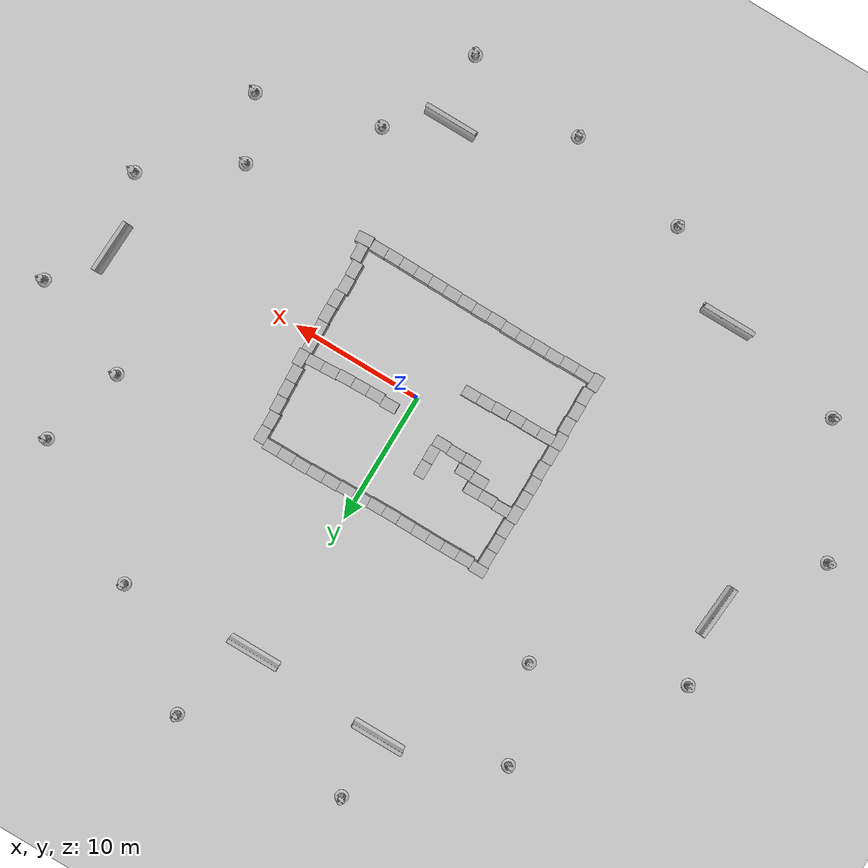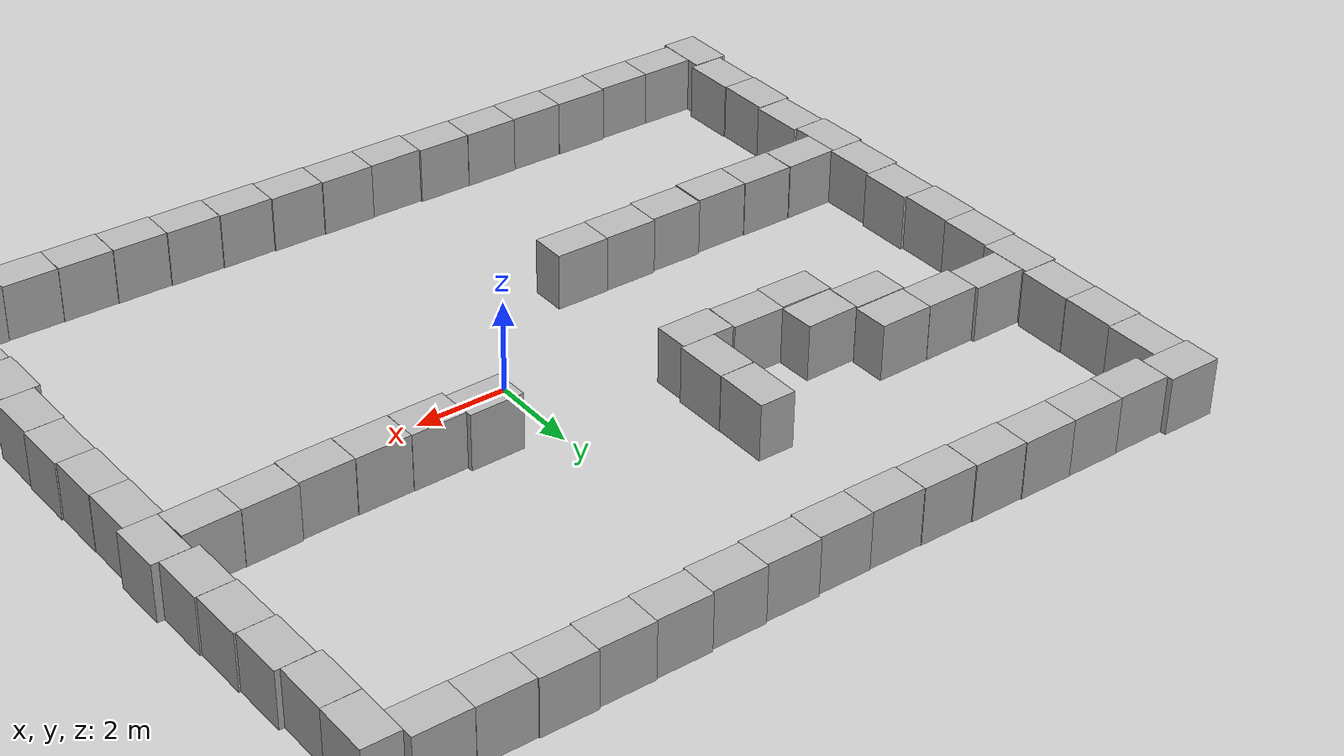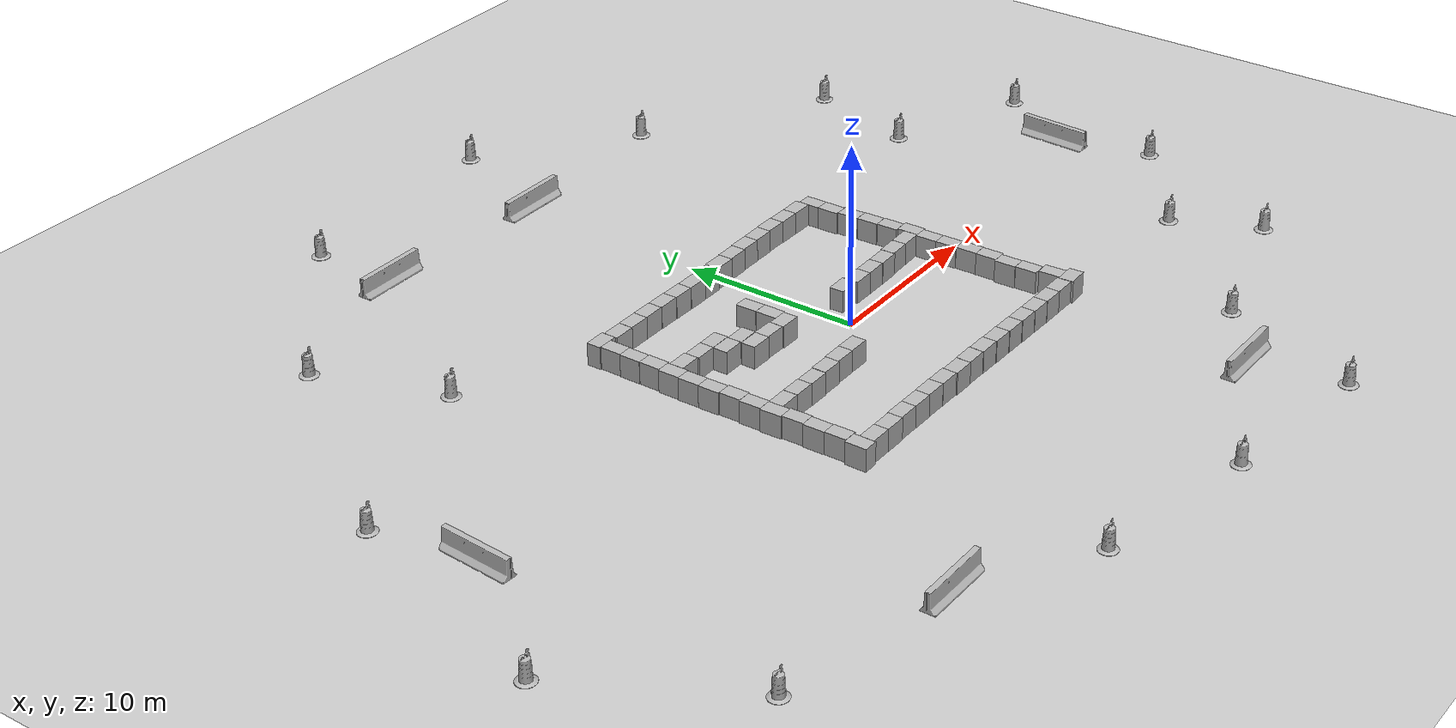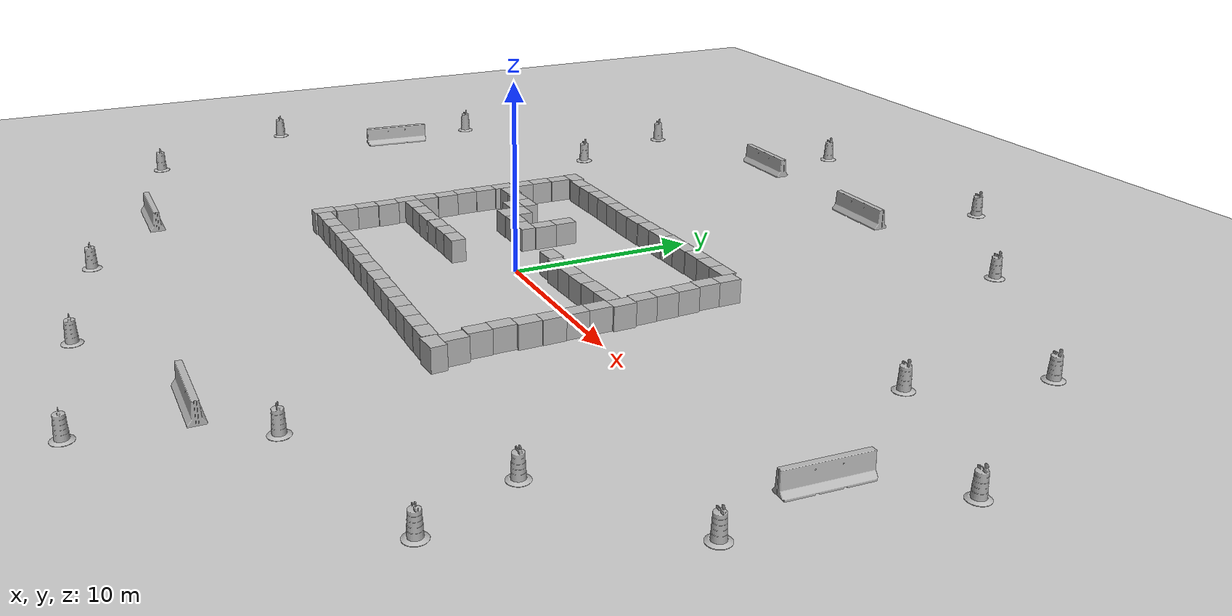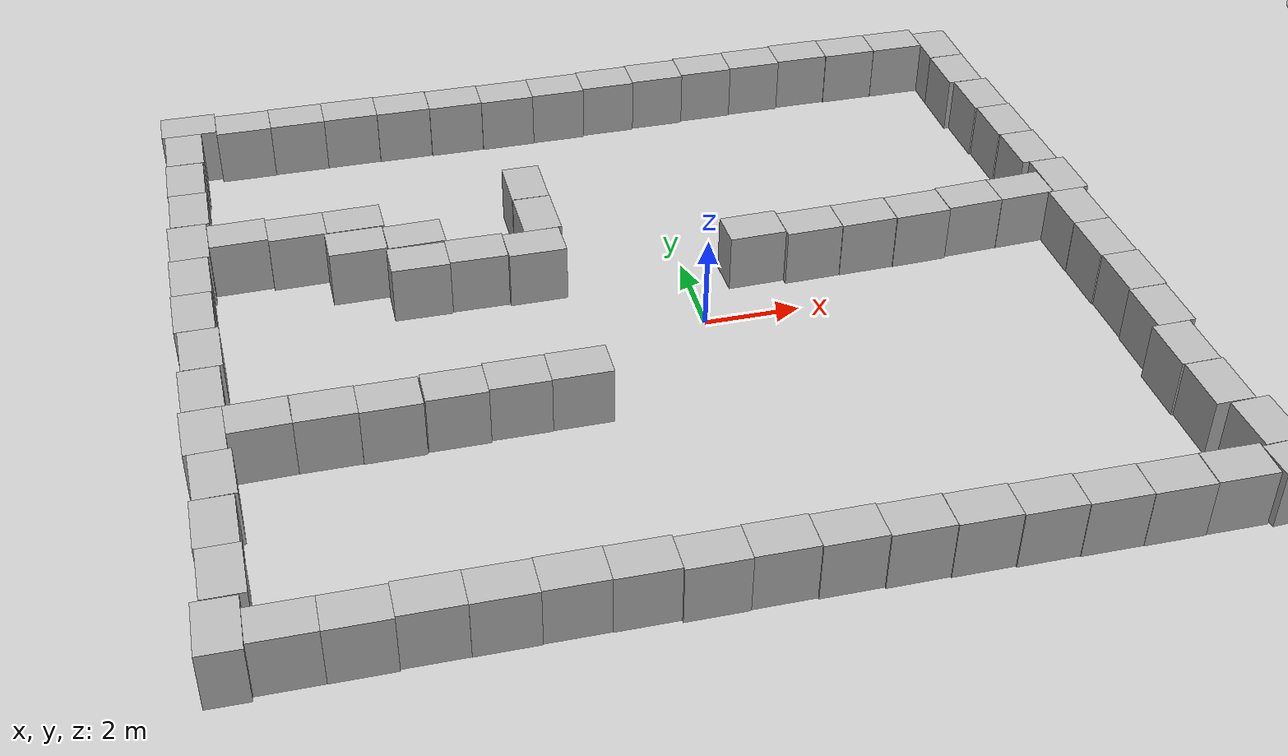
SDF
<sdf version="1.7">
 <world name="default">
  <light name="sun" type="directional">
   <pose>0 0 10 0 -0 0</pose>
   <diffuse>0.8 0.8 0.8 1</diffuse>
   <specular>0.2 0.2 0.2 1</specular>
   <attenuation>
    <range>1000</range>
    <constant>0.9</constant>
    <linear>0.01</linear>
    <quadratic>0.001</quadratic>
   </attenuation>
   <direction>-0.5 0.1 -0.9</direction>
   <spot><inner_angle>0</inner_angle><outer_angle>0</outer_angle><falloff>0</falloff></spot>
  </light>
  <model name="ground_plane">
   <static>1</static>
   <link name="link">
    <collision name="collision">
     <geometry><plane><normal>0 0 1</normal><size>100 100</size></plane></geometry>
     <surface><friction><ode><mu>100</mu><mu2>50</mu2></ode></friction></surface>
    </collision>
    <visual name="visual">
     <cast_shadows>0</cast_shadows>
     <geometry><plane><normal>0 0 1</normal><size>100 100</size></plane></geometry>
     <material>
      <script><uri>file://media/materials/scripts/gazebo.material</uri><name>Gazebo/Grey</name></script>
     </material>
    </visual>
    <velocity_decay><linear>0</linear><angular>0</angular></velocity_decay>
   </link>
  </model>
  <physics type="ode">
   <max_step_size>0.001</max_step_size>
   <real_time_factor>1</real_time_factor>
   <real_time_update_rate>1000</real_time_update_rate>
  </physics>
  <scene><ambient>0.4 0.4 0.4 1</ambient><background>0.7 0.7 0.7 1</background><shadows>1</shadows></scene>
  <spherical_coordinates>
   <surface_model>EARTH_WGS84</surface_model>
   <latitude_deg>0</latitude_deg>
   <longitude_deg>0</longitude_deg>
   <elevation>0</elevation>
   <heading_deg>0</heading_deg>
  </spherical_coordinates>
  <model name="Construction Barrel">
   <link name="link">
    <inertial>
     <pose>0 0 0.4 0 -0 0</pose>
     <mass>500</mass>
     <inertia><ixx>51.2096</ixx><iyy>51.2096</iyy><izz>25</izz><ixy>0</ixy><ixz>0</ixz><iyz>0</iyz></inertia>
    </inertial>
    <collision name="collision">
     <geometry><mesh><uri>model://construction_barrel/meshes/construction_barrel.dae</uri></mesh></geometry>
    </collision>
    <visual name="visual">
     <geometry><mesh><uri>model://construction_barrel/meshes/construction_barrel.dae</uri></mesh></geometry>
    </visual>
    <velocity_decay><linear>0</linear><angular>0</angular></velocity_decay>
   </link>
   <pose>-0.251054 -21.8083 0 0 0 -0.002184</pose>
   <static>0</static>
  </model>
  <model name="Construction Barrel_0">
   <link name="link">
    <inertial>
     <pose>0 0 0.4 0 -0 0</pose>
     <mass>500</mass>
     <inertia><ixx>51.2096</ixx><iyy>51.2096</iyy><izz>25</izz><ixy>0</ixy><ixz>0</ixz><iyz>0</iyz></inertia>
    </inertial>
    <collision name="collision">
     <geometry><mesh><uri>model://construction_barrel/meshes/construction_barrel.dae</uri></mesh></geometry>
    </collision>
    <visual name="visual">
     <geometry><mesh><uri>model://construction_barrel/meshes/construction_barrel.dae</uri></mesh></geometry>
    </visual>
    <velocity_decay><linear>0</linear><angular>0</angular></velocity_decay>
   </link>
   <pose>12.0468 -15.209 0 0 0 -0.002197</pose>
   <static>0</static>
  </model>
  <model name="Construction Barrel_1">
   <link name="link">
    <inertial>
     <pose>0 0 0.4 0 -0 0</pose>
     <mass>500</mass>
     <inertia><ixx>51.2096</ixx><iyy>51.2096</iyy><izz>25</izz><ixy>0</ixy><ixz>0</ixz><iyz>0</iyz></inertia>
    </inertial>
    <collision name="collision">
     <geometry><mesh><uri>model://construction_barrel/meshes/construction_barrel.dae</uri></mesh></geometry>
    </collision>
    <visual name="visual">
     <geometry><mesh><uri>model://construction_barrel/meshes/construction_barrel.dae</uri></mesh></geometry>
    </visual>
    <velocity_decay><linear>0</linear><angular>0</angular></velocity_decay>
   </link>
   <pose>18.9997 -7.99906 0 0 0 -0.00214</pose>
   <static>0</static>
  </model>
  <model name="Construction Barrel_2">
   <link name="link">
    <inertial>
     <pose>0 0 0.4 0 -0 0</pose>
     <mass>500</mass>
     <inertia><ixx>51.2096</ixx><iyy>51.2096</iyy><izz>25</izz><ixy>0</ixy><ixz>0</ixz><iyz>0</iyz></inertia>
    </inertial>
    <collision name="collision">
     <geometry><mesh><uri>model://construction_barrel/meshes/construction_barrel.dae</uri></mesh></geometry>
    </collision>
    <visual name="visual">
     <geometry><mesh><uri>model://construction_barrel/meshes/construction_barrel.dae</uri></mesh></geometry>
    </visual>
    <velocity_decay><linear>0</linear><angular>0</angular></velocity_decay>
   </link>
   <pose>-16.5173 12.0056 0 0 0 -0.002074</pose>
   <static>0</static>
  </model>
  <model name="Construction Barrel_3">
   <link name="link">
    <inertial>
     <pose>0 0 0.4 0 -0 0</pose>
     <mass>500</mass>
     <inertia><ixx>51.2096</ixx><iyy>51.2096</iyy><izz>25</izz><ixy>0</ixy><ixz>0</ixz><iyz>0</iyz></inertia>
    </inertial>
    <collision name="collision">
     <geometry><mesh><uri>model://construction_barrel/meshes/construction_barrel.dae</uri></mesh></geometry>
    </collision>
    <visual name="visual">
     <geometry><mesh><uri>model://construction_barrel/meshes/construction_barrel.dae</uri></mesh></geometry>
    </visual>
    <velocity_decay><linear>0</linear><angular>0</angular></velocity_decay>
   </link>
   <pose>19.1339 9.52281 0 0 0 -0.001991</pose>
   <static>0</static>
  </model>
  <model name="Construction Barrel_4">
   <link name="link">
    <inertial>
     <pose>0 0 0.4 0 -0 0</pose>
     <mass>500</mass>
     <inertia><ixx>51.2096</ixx><iyy>51.2096</iyy><izz>25</izz><ixy>0</ixy><ixz>0</ixz><iyz>0</iyz></inertia>
    </inertial>
    <collision name="collision">
     <geometry><mesh><uri>model://construction_barrel/meshes/construction_barrel.dae</uri></mesh></geometry>
    </collision>
    <visual name="visual">
     <geometry><mesh><uri>model://construction_barrel/meshes/construction_barrel.dae</uri></mesh></geometry>
    </visual>
    <velocity_decay><linear>0</linear><angular>0</angular></velocity_decay>
   </link>
   <pose>25.433 -3.40529 0 0 0 -0.001879</pose>
   <static>0</static>
  </model>
  <model name="Construction Barrel_5">
   <link name="link">
    <inertial>
     <pose>0 0 0.4 0 -0 0</pose>
     <mass>500</mass>
     <inertia><ixx>51.2096</ixx><iyy>51.2096</iyy><izz>25</izz><ixy>0</ixy><ixz>0</ixz><iyz>0</iyz></inertia>
    </inertial>
    <collision name="collision">
     <geometry><mesh><uri>model://construction_barrel/meshes/construction_barrel.dae</uri></mesh></geometry>
    </collision>
    <visual name="visual">
     <geometry><mesh><uri>model://construction_barrel/meshes/construction_barrel.dae</uri></mesh></geometry>
    </visual>
    <velocity_decay><linear>0</linear><angular>0</angular></velocity_decay>
   </link>
   <pose>-27.0002 7.54608 0 0 0 -0.001826</pose>
   <static>0</static>
  </model>
  <model name="Construction Barrel_6">
   <link name="link">
    <inertial>
     <pose>0 0 0.4 0 -0 0</pose>
     <mass>500</mass>
     <inertia><ixx>51.2096</ixx><iyy>51.2096</iyy><izz>25</izz><ixy>0</ixy><ixz>0</ixz><iyz>0</iyz></inertia>
    </inertial>
    <collision name="collision">
     <geometry><mesh><uri>model://construction_barrel/meshes/construction_barrel.dae</uri></mesh></geometry>
    </collision>
    <visual name="visual">
     <geometry><mesh><uri>model://construction_barrel/meshes/construction_barrel.dae</uri></mesh></geometry>
    </visual>
    <velocity_decay><linear>0</linear><angular>0</angular></velocity_decay>
   </link>
   <pose>-10.0002 27.0007 0 0 0 -0.00183</pose>
   <static>0</static>
  </model>
  <model name="Construction Barrel_7">
   <link name="link">
    <inertial>
     <pose>0 0 0.4 0 -0 0</pose>
     <mass>500</mass>
     <inertia><ixx>51.2096</ixx><iyy>51.2096</iyy><izz>25</izz><ixy>0</ixy><ixz>0</ixz><iyz>0</iyz></inertia>
    </inertial>
    <collision name="collision">
     <geometry><mesh><uri>model://construction_barrel/meshes/construction_barrel.dae</uri></mesh></geometry>
    </collision>
    <visual name="visual">
     <geometry><mesh><uri>model://construction_barrel/meshes/construction_barrel.dae</uri></mesh></geometry>
    </visual>
    <velocity_decay><linear>0</linear><angular>0</angular></velocity_decay>
   </link>
   <pose>-31.0002 -4.99928 0 0 0 -0.001746</pose>
   <static>0</static>
  </model>
  <model name="Construction Barrel_8">
   <link name="link">
    <inertial>
     <pose>0 0 0.4 0 -0 0</pose>
     <mass>500</mass>
     <inertia><ixx>51.2096</ixx><iyy>51.2096</iyy><izz>25</izz><ixy>0</ixy><ixz>0</ixz><iyz>0</iyz></inertia>
    </inertial>
    <collision name="collision">
     <geometry><mesh><uri>model://construction_barrel/meshes/construction_barrel.dae</uri></mesh></geometry>
    </collision>
    <visual name="visual">
     <geometry><mesh><uri>model://construction_barrel/meshes/construction_barrel.dae</uri></mesh></geometry>
    </visual>
    <velocity_decay><linear>0</linear><angular>0</angular></velocity_decay>
   </link>
   <pose>-9.56833 -19.9993 0 0 0 -0.001691</pose>
   <static>0</static>
  </model>
  <model name="Construction Barrel_9">
   <link name="link">
    <inertial>
     <pose>0 0 0.4 0 -0 0</pose>
     <mass>500</mass>
     <inertia><ixx>51.2096</ixx><iyy>51.2096</iyy><izz>25</izz><ixy>0</ixy><ixz>0</ixz><iyz>0</iyz></inertia>
    </inertial>
    <collision name="collision">
     <geometry><mesh><uri>model://construction_barrel/meshes/construction_barrel.dae</uri></mesh></geometry>
    </collision>
    <visual name="visual">
     <geometry><mesh><uri>model://construction_barrel/meshes/construction_barrel.dae</uri></mesh></geometry>
    </visual>
    <velocity_decay><linear>0</linear><angular>0</angular></velocity_decay>
   </link>
   <pose>-26.0003 -13.9994 0 0 0 -0.001597</pose>
   <static>0</static>
  </model>
  <model name="Construction Barrel_10">
   <link name="link">
    <inertial>
     <pose>0 0 0.4 0 -0 0</pose>
     <mass>500</mass>
     <inertia><ixx>51.2096</ixx><iyy>51.2096</iyy><izz>25</izz><ixy>0</ixy><ixz>0</ixz><iyz>0</iyz></inertia>
    </inertial>
    <collision name="collision">
     <geometry><mesh><uri>model://construction_barrel/meshes/construction_barrel.dae</uri></mesh></geometry>
    </collision>
    <visual name="visual">
     <geometry><mesh><uri>model://construction_barrel/meshes/construction_barrel.dae</uri></mesh></geometry>
    </visual>
    <velocity_decay><linear>0</linear><angular>0</angular></velocity_decay>
   </link>
   <pose>8.99978 -22.9994 -2e-06 -7e-06 -4e-06 -0.001559</pose>
   <static>0</static>
  </model>
  <model name="Construction Barrel_11">
   <link name="link">
    <inertial>
     <pose>0 0 0.4 0 -0 0</pose>
     <mass>500</mass>
     <inertia><ixx>51.2096</ixx><iyy>51.2096</iyy><izz>25</izz><ixy>0</ixy><ixz>0</ixz><iyz>0</iyz></inertia>
    </inertial>
    <collision name="collision">
     <geometry><mesh><uri>model://construction_barrel/meshes/construction_barrel.dae</uri></mesh></geometry>
    </collision>
    <visual name="visual">
     <geometry><mesh><uri>model://construction_barrel/meshes/construction_barrel.dae</uri></mesh></geometry>
    </visual>
    <velocity_decay><linear>0</linear><angular>0</angular></velocity_decay>
   </link>
   <pose>10.9997 22.0005 -2e-06 -7e-06 -4e-06 -0.001508</pose>
   <static>0</static>
  </model>
  <model name="Construction Barrel_12">
   <link name="link">
    <inertial>
     <pose>0 0 0.4 0 -0 0</pose>
     <mass>500</mass>
     <inertia><ixx>51.2096</ixx><iyy>51.2096</iyy><izz>25</izz><ixy>0</ixy><ixz>0</ixz><iyz>0</iyz></inertia>
    </inertial>
    <collision name="collision">
     <geometry><mesh><uri>model://construction_barrel/meshes/construction_barrel.dae</uri></mesh></geometry>
    </collision>
    <visual name="visual">
     <geometry><mesh><uri>model://construction_barrel/meshes/construction_barrel.dae</uri></mesh></geometry>
    </visual>
    <velocity_decay><linear>0</linear><angular>0</angular></velocity_decay>
   </link>
   <pose>26.9997 6.44779 0 0 0 -0.001438</pose>
   <static>0</static>
  </model>
  <model name="Construction Barrel_13">
   <link name="link">
    <inertial>
     <pose>0 0 0.4 0 -0 0</pose>
     <mass>500</mass>
     <inertia><ixx>51.2096</ixx><iyy>51.2096</iyy><izz>25</izz><ixy>0</ixy><ixz>0</ixz><iyz>0</iyz></inertia>
    </inertial>
    <collision name="collision">
     <geometry><mesh><uri>model://construction_barrel/meshes/construction_barrel.dae</uri></mesh></geometry>
    </collision>
    <visual name="visual">
     <geometry><mesh><uri>model://construction_barrel/meshes/construction_barrel.dae</uri></mesh></geometry>
    </visual>
    <velocity_decay><linear>0</linear><angular>0</angular></velocity_decay>
   </link>
   <pose>21.0308 -12.6725 -1e-06 0 5e-06 -0.001347</pose>
   <static>0</static>
  </model>
  <model name="Construction Barrel_14">
   <link name="link">
    <inertial>
     <pose>0 0 0.4 0 -0 0</pose>
     <mass>500</mass>
     <inertia><ixx>51.2096</ixx><iyy>51.2096</iyy><izz>25</izz><ixy>0</ixy><ixz>0</ixz><iyz>0</iyz></inertia>
    </inertial>
    <collision name="collision">
     <geometry><mesh><uri>model://construction_barrel/meshes/construction_barrel.dae</uri></mesh></geometry>
    </collision>
    <visual name="visual">
     <geometry><mesh><uri>model://construction_barrel/meshes/construction_barrel.dae</uri></mesh></geometry>
    </visual>
    <velocity_decay><linear>0</linear><angular>0</angular></velocity_decay>
   </link>
   <pose>-19.0002 19.0004 -1e-06 0 5e-06 -0.001311</pose>
   <static>0</static>
  </model>
  <model name="Construction Barrel_15">
   <link name="link">
    <inertial>
     <pose>0 0 0.4 0 -0 0</pose>
     <mass>500</mass>
     <inertia><ixx>51.2096</ixx><iyy>51.2096</iyy><izz>25</izz><ixy>0</ixy><ixz>0</ixz><iyz>0</iyz></inertia>
    </inertial>
    <collision name="collision">
     <geometry><mesh><uri>model://construction_barrel/meshes/construction_barrel.dae</uri></mesh></geometry>
    </collision>
    <visual name="visual">
     <geometry><mesh><uri>model://construction_barrel/meshes/construction_barrel.dae</uri></mesh></geometry>
    </visual>
    <velocity_decay><linear>0</linear><angular>0</angular></velocity_decay>
   </link>
   <pose>20.9998 16.0004 -1e-06 -0 5e-06 -0.001248</pose>
   <static>0</static>
  </model>
  <model name="Construction Barrel_16">
   <link name="link">
    <inertial>
     <pose>0 0 0.4 0 -0 0</pose>
     <mass>500</mass>
     <inertia><ixx>51.2096</ixx><iyy>51.2096</iyy><izz>25</izz><ixy>0</ixy><ixz>0</ixz><iyz>0</iyz></inertia>
    </inertial>
    <collision name="collision">
     <geometry><mesh><uri>model://construction_barrel/meshes/construction_barrel.dae</uri></mesh></geometry>
    </collision>
    <visual name="visual">
     <geometry><mesh><uri>model://construction_barrel/meshes/construction_barrel.dae</uri></mesh></geometry>
    </visual>
    <velocity_decay><linear>0</linear><angular>0</angular></velocity_decay>
   </link>
   <pose>2.99981 28.0004 -1e-06 0 5e-06 -0.001185</pose>
   <static>0</static>
  </model>
  <model name="jersey_barrier">
   <static>1</static>
   <link name="link">
    <visual name="visual">
     <geometry><mesh><uri>model://jersey_barrier/meshes/jersey_barrier.dae</uri></mesh></geometry>
    </visual>
    <collision name="upright">
     <pose>0 0 0.5715 0 -0 0</pose>
     <geometry><box><size>4.06542 0.3063 1.143</size></box></geometry>
    </collision>
    <collision name="base">
     <pose>0 0 0.032258 0 -0 0</pose>
     <geometry><box><size>4.06542 0.8107 0.064516</size></box></geometry>
    </collision>
    <collision name="base2">
     <pose>0 0 0.1 0 -0 0</pose>
     <geometry><box><size>4.06542 0.65 0.1</size></box></geometry>
    </collision>
    <collision name="base3">
     <pose>0 0 0.2 0 -0 0</pose>
     <geometry><box><size>4.06542 0.5 0.1</size></box></geometry>
    </collision>
    <collision name="left-angle">
     <pose>0 -0.224 0.2401 0.9 -0 0</pose>
     <geometry><box><size>4.06542 0.5 0.064516</size></box></geometry>
    </collision>
    <collision name="right-angle">
     <pose>0 0.224 0.2401 -0.9 0 0</pose>
     <geometry><box><size>4.06542 0.5 0.064516</size></box></geometry>
    </collision>
    <velocity_decay><linear>0</linear><angular>0</angular></velocity_decay>
   </link>
   <pose>0.597215 21.4103 0 0 -0 0</pose>
  </model>
  <model name="jersey_barrier_0">
   <static>1</static>
   <link name="link">
    <visual name="visual">
     <geometry><mesh><uri>model://jersey_barrier/meshes/jersey_barrier.dae</uri></mesh></geometry>
    </visual>
    <collision name="upright">
     <pose>0 0 0.5715 0 -0 0</pose>
     <geometry><box><size>4.06542 0.3063 1.143</size></box></geometry>
    </collision>
    <collision name="base">
     <pose>0 0 0.032258 0 -0 0</pose>
     <geometry><box><size>4.06542 0.8107 0.064516</size></box></geometry>
    </collision>
    <collision name="base2">
     <pose>0 0 0.1 0 -0 0</pose>
     <geometry><box><size>4.06542 0.65 0.1</size></box></geometry>
    </collision>
    <collision name="base3">
     <pose>0 0 0.2 0 -0 0</pose>
     <geometry><box><size>4.06542 0.5 0.1</size></box></geometry>
    </collision>
    <collision name="left-angle">
     <pose>0 -0.224 0.2401 0.9 -0 0</pose>
     <geometry><box><size>4.06542 0.5 0.064516</size></box></geometry>
    </collision>
    <collision name="right-angle">
     <pose>0 0.224 0.2401 -0.9 0 0</pose>
     <geometry><box><size>4.06542 0.5 0.064516</size></box></geometry>
    </collision>
    <velocity_decay><linear>0</linear><angular>0</angular></velocity_decay>
   </link>
   <pose>-10 22 0 0 -0 0</pose>
  </model>
  <model name="jersey_barrier_1">
   <static>1</static>
   <link name="link">
    <visual name="visual">
     <geometry><mesh><uri>model://jersey_barrier/meshes/jersey_barrier.dae</uri></mesh></geometry>
    </visual>
    <collision name="upright">
     <pose>0 0 0.5715 0 -0 0</pose>
     <geometry><box><size>4.06542 0.3063 1.143</size></box></geometry>
    </collision>
    <collision name="base">
     <pose>0 0 0.032258 0 -0 0</pose>
     <geometry><box><size>4.06542 0.8107 0.064516</size></box></geometry>
    </collision>
    <collision name="base2">
     <pose>0 0 0.1 0 -0 0</pose>
     <geometry><box><size>4.06542 0.65 0.1</size></box></geometry>
    </collision>
    <collision name="base3">
     <pose>0 0 0.2 0 -0 0</pose>
     <geometry><box><size>4.06542 0.5 0.1</size></box></geometry>
    </collision>
    <collision name="left-angle">
     <pose>0 -0.224 0.2401 0.9 -0 0</pose>
     <geometry><box><size>4.06542 0.5 0.064516</size></box></geometry>
    </collision>
    <collision name="right-angle">
     <pose>0 0.224 0.2401 -0.9 0 0</pose>
     <geometry><box><size>4.06542 0.5 0.064516</size></box></geometry>
    </collision>
    <velocity_decay><linear>0</linear><angular>0</angular></velocity_decay>
   </link>
   <pose>-26 2 0 0 -0 1.49459</pose>
  </model>
  <model name="jersey_barrier_2">
   <static>1</static>
   <link name="link">
    <visual name="visual">
     <geometry><mesh><uri>model://jersey_barrier/meshes/jersey_barrier.dae</uri></mesh></geometry>
    </visual>
    <collision name="upright">
     <pose>0 0 0.5715 0 -0 0</pose>
     <geometry><box><size>4.06542 0.3063 1.143</size></box></geometry>
    </collision>
    <collision name="base">
     <pose>0 0 0.032258 0 -0 0</pose>
     <geometry><box><size>4.06542 0.8107 0.064516</size></box></geometry>
    </collision>
    <collision name="base2">
     <pose>0 0 0.1 0 -0 0</pose>
     <geometry><box><size>4.06542 0.65 0.1</size></box></geometry>
    </collision>
    <collision name="base3">
     <pose>0 0 0.2 0 -0 0</pose>
     <geometry><box><size>4.06542 0.5 0.1</size></box></geometry>
    </collision>
    <collision name="left-angle">
     <pose>0 -0.224 0.2401 0.9 -0 0</pose>
     <geometry><box><size>4.06542 0.5 0.064516</size></box></geometry>
    </collision>
    <collision name="right-angle">
     <pose>0 0.224 0.2401 -0.9 0 0</pose>
     <geometry><box><size>4.06542 0.5 0.064516</size></box></geometry>
    </collision>
    <velocity_decay><linear>0</linear><angular>0</angular></velocity_decay>
   </link>
   <pose>-16 -16 0 0 -0 0</pose>
  </model>
  <model name="jersey_barrier_3">
   <static>1</static>
   <link name="link">
    <visual name="visual">
     <geometry><mesh><uri>model://jersey_barrier/meshes/jersey_barrier.dae</uri></mesh></geometry>
    </visual>
    <collision name="upright">
     <pose>0 0 0.5715 0 -0 0</pose>
     <geometry><box><size>4.06542 0.3063 1.143</size></box></geometry>
    </collision>
    <collision name="base">
     <pose>0 0 0.032258 0 -0 0</pose>
     <geometry><box><size>4.06542 0.8107 0.064516</size></box></geometry>
    </collision>
    <collision name="base2">
     <pose>0 0 0.1 0 -0 0</pose>
     <geometry><box><size>4.06542 0.65 0.1</size></box></geometry>
    </collision>
    <collision name="base3">
     <pose>0 0 0.2 0 -0 0</pose>
     <geometry><box><size>4.06542 0.5 0.1</size></box></geometry>
    </collision>
    <collision name="left-angle">
     <pose>0 -0.224 0.2401 0.9 -0 0</pose>
     <geometry><box><size>4.06542 0.5 0.064516</size></box></geometry>
    </collision>
    <collision name="right-angle">
     <pose>0 0.224 0.2401 -0.9 0 0</pose>
     <geometry><box><size>4.06542 0.5 0.064516</size></box></geometry>
    </collision>
    <velocity_decay><linear>0</linear><angular>0</angular></velocity_decay>
   </link>
   <pose>8 -18 0 0 -0 0</pose>
  </model>
  <model name="jersey_barrier_4">
   <static>1</static>
   <link name="link">
    <visual name="visual">
     <geometry><mesh><uri>model://jersey_barrier/meshes/jersey_barrier.dae</uri></mesh></geometry>
    </visual>
    <collision name="upright">
     <pose>0 0 0.5715 0 -0 0</pose>
     <geometry><box><size>4.06542 0.3063 1.143</size></box></geometry>
    </collision>
    <collision name="base">
     <pose>0 0 0.032258 0 -0 0</pose>
     <geometry><box><size>4.06542 0.8107 0.064516</size></box></geometry>
    </collision>
    <collision name="base2">
     <pose>0 0 0.1 0 -0 0</pose>
     <geometry><box><size>4.06542 0.65 0.1</size></box></geometry>
    </collision>
    <collision name="base3">
     <pose>0 0 0.2 0 -0 0</pose>
     <geometry><box><size>4.06542 0.5 0.1</size></box></geometry>
    </collision>
    <collision name="left-angle">
     <pose>0 -0.224 0.2401 0.9 -0 0</pose>
     <geometry><box><size>4.06542 0.5 0.064516</size></box></geometry>
    </collision>
    <collision name="right-angle">
     <pose>0 0.224 0.2401 -0.9 0 0</pose>
     <geometry><box><size>4.06542 0.5 0.064516</size></box></geometry>
    </collision>
    <velocity_decay><linear>0</linear><angular>0</angular></velocity_decay>
   </link>
   <pose>24 2 0 0 -0 1.52298</pose>
  </model>
  <gravity>0 0 -9.8</gravity>
  <magnetic_field>6e-06 2.3e-05 -4.2e-05</magnetic_field>
  <atmosphere type="adiabatic"/>
  <model name="Big box 4">
   <pose>-0.791601 -7.48336 0.624645 0.000738 9.8e-05 0.00236</pose>
   <static>0</static>
   <link name="link">
    <inertial>
     <mass>40</mass>
     <inertia><ixx>1</ixx><ixy>0</ixy><ixz>0</ixz><iyy>1</iyy><iyz>0</iyz><izz>1</izz></inertia>
    </inertial>
    <collision name="collision">
     <geometry><box><size>1.2 0.8 1.25</size></box></geometry>
     <surface><contact><ode><max_vel>0.1</max_vel><min_depth>0.001</min_depth></ode></contact></surface>
    </collision>
    <visual name="visual">
     <geometry><mesh><uri>model://big_box4/meshes/big_box.dae</uri></mesh></geometry>
    </visual>
   </link>
  </model>
  <model name="Big box 4_clone">
   <pose>0.409447 -7.50658 0.624907 -0.000228 -2e-06 0.005854</pose>
   <static>0</static>
   <link name="link">
    <inertial>
     <mass>40</mass>
     <inertia><ixx>1</ixx><ixy>0</ixy><ixz>0</ixz><iyy>1</iyy><iyz>0</iyz><izz>1</izz></inertia>
    </inertial>
    <collision name="collision">
     <geometry><box><size>1.2 0.8 1.25</size></box></geometry>
     <surface><contact><ode><max_vel>0.1</max_vel><min_depth>0.001</min_depth></ode></contact></surface>
    </collision>
    <visual name="visual">
     <geometry><mesh><uri>model://big_box4/meshes/big_box.dae</uri></mesh></geometry>
    </visual>
   </link>
  </model>
  <model name="Big box 4_clone_0">
   <pose>1.60953 -7.5337 0.624856 0.00057 0.000152 0.005839</pose>
   <static>0</static>
   <link name="link">
    <inertial>
     <mass>40</mass>
     <inertia><ixx>1</ixx><ixy>0</ixy><ixz>0</ixz><iyy>1</iyy><iyz>0</iyz><izz>1</izz></inertia>
    </inertial>
    <collision name="collision">
     <geometry><box><size>1.2 0.8 1.25</size></box></geometry>
     <surface><contact><ode><max_vel>0.1</max_vel><min_depth>0.001</min_depth></ode></contact></surface>
    </collision>
    <visual name="visual">
     <geometry><mesh><uri>model://big_box4/meshes/big_box.dae</uri></mesh></geometry>
    </visual>
   </link>
  </model>
  <model name="Big box 4_clone_1">
   <pose>2.81246 -7.54962 0.624549 0 0.000466 0.002697</pose>
   <static>0</static>
   <link name="link">
    <inertial>
     <mass>40</mass>
     <inertia><ixx>1</ixx><ixy>0</ixy><ixz>0</ixz><iyy>1</iyy><iyz>0</iyz><izz>1</izz></inertia>
    </inertial>
    <collision name="collision">
     <geometry><box><size>1.2 0.8 1.25</size></box></geometry>
     <surface><contact><ode><max_vel>0.1</max_vel><min_depth>0.001</min_depth></ode></contact></surface>
    </collision>
    <visual name="visual">
     <geometry><mesh><uri>model://big_box4/meshes/big_box.dae</uri></mesh></geometry>
    </visual>
   </link>
  </model>
  <model name="Big box 4_clone_2">
   <pose>4.0136 -7.574 0.624498 0 -0.000831 0.002003</pose>
   <static>0</static>
   <link name="link">
    <inertial>
     <mass>40</mass>
     <inertia><ixx>1</ixx><ixy>0</ixy><ixz>0</ixz><iyy>1</iyy><iyz>0</iyz><izz>1</izz></inertia>
    </inertial>
    <collision name="collision">
     <geometry><box><size>1.2 0.8 1.25</size></box></geometry>
     <surface><contact><ode><max_vel>0.1</max_vel><min_depth>0.001</min_depth></ode></contact></surface>
    </collision>
    <visual name="visual">
     <geometry><mesh><uri>model://big_box4/meshes/big_box.dae</uri></mesh></geometry>
    </visual>
   </link>
  </model>
  <model name="Big box 4_clone_3">
   <pose>5.21501 -7.59105 0.624499 0 -0.000831 -0.00103</pose>
   <static>0</static>
   <link name="link">
    <inertial>
     <mass>40</mass>
     <inertia><ixx>1</ixx><ixy>0</ixy><ixz>0</ixz><iyy>1</iyy><iyz>0</iyz><izz>1</izz></inertia>
    </inertial>
    <collision name="collision">
     <geometry><box><size>1.2 0.8 1.25</size></box></geometry>
     <surface><contact><ode><max_vel>0.1</max_vel><min_depth>0.001</min_depth></ode></contact></surface>
    </collision>
    <visual name="visual">
     <geometry><mesh><uri>model://big_box4/meshes/big_box.dae</uri></mesh></geometry>
    </visual>
   </link>
  </model>
  <model name="Big box 4_clone_4">
   <pose>6.41592 -7.60311 0.6245 -0.001244 -3e-06 -0.001878</pose>
   <static>0</static>
   <link name="link">
    <inertial>
     <mass>40</mass>
     <inertia><ixx>1</ixx><ixy>0</ixy><ixz>0</ixz><iyy>1</iyy><iyz>0</iyz><izz>1</izz></inertia>
    </inertial>
    <collision name="collision">
     <geometry><box><size>1.2 0.8 1.25</size></box></geometry>
     <surface><contact><ode><max_vel>0.1</max_vel><min_depth>0.001</min_depth></ode></contact></surface>
    </collision>
    <visual name="visual">
     <geometry><mesh><uri>model://big_box4/meshes/big_box.dae</uri></mesh></geometry>
    </visual>
   </link>
  </model>
  <model name="Big box 4_clone_5">
   <pose>-1.99145 -7.50285 0.624587 -0.001032 0 0.001057</pose>
   <static>0</static>
   <link name="link">
    <inertial>
     <mass>40</mass>
     <inertia><ixx>1</ixx><ixy>0</ixy><ixz>0</ixz><iyy>1</iyy><iyz>0</iyz><izz>1</izz></inertia>
    </inertial>
    <collision name="collision">
     <geometry><box><size>1.2 0.8 1.25</size></box></geometry>
     <surface><contact><ode><max_vel>0.1</max_vel><min_depth>0.001</min_depth></ode></contact></surface>
    </collision>
    <visual name="visual">
     <geometry><mesh><uri>model://big_box4/meshes/big_box.dae</uri></mesh></geometry>
    </visual>
   </link>
  </model>
  <model name="Big box 4_clone_6">
   <pose>-3.19129 -7.44955 0.624831 1e-06 -0.000282 -0.000412</pose>
   <static>0</static>
   <link name="link">
    <inertial>
     <mass>40</mass>
     <inertia><ixx>1</ixx><ixy>0</ixy><ixz>0</ixz><iyy>1</iyy><iyz>0</iyz><izz>1</izz></inertia>
    </inertial>
    <collision name="collision">
     <geometry><box><size>1.2 0.8 1.25</size></box></geometry>
     <surface><contact><ode><max_vel>0.1</max_vel><min_depth>0.001</min_depth></ode></contact></surface>
    </collision>
    <visual name="visual">
     <geometry><mesh><uri>model://big_box4/meshes/big_box.dae</uri></mesh></geometry>
    </visual>
   </link>
  </model>
  <model name="Big box 4_clone_4_clone">
   <pose>7.62341 -7.59497 0.624499 -0.001241 -6e-06 -0.002668</pose>
   <static>0</static>
   <link name="link">
    <inertial>
     <mass>40</mass>
     <inertia><ixx>1</ixx><ixy>0</ixy><ixz>0</ixz><iyy>1</iyy><iyz>0</iyz><izz>1</izz></inertia>
    </inertial>
    <collision name="collision">
     <geometry><box><size>1.2 0.8 1.25</size></box></geometry>
     <surface><contact><ode><max_vel>0.1</max_vel><min_depth>0.001</min_depth></ode></contact></surface>
    </collision>
    <visual name="visual">
     <geometry><mesh><uri>model://big_box4/meshes/big_box.dae</uri></mesh></geometry>
    </visual>
   </link>
  </model>
  <model name="Big box 4_clone_4_clone_0">
   <pose>8.8511 -7.64855 0.624536 0 0.000758 0.065908</pose>
   <static>0</static>
   <link name="link">
    <inertial>
     <mass>40</mass>
     <inertia><ixx>1</ixx><ixy>0</ixy><ixz>0</ixz><iyy>1</iyy><iyz>0</iyz><izz>1</izz></inertia>
    </inertial>
    <collision name="collision">
     <geometry><box><size>1.2 0.8 1.25</size></box></geometry>
     <surface><contact><ode><max_vel>0.1</max_vel><min_depth>0.001</min_depth></ode></contact></surface>
    </collision>
    <visual name="visual">
     <geometry><mesh><uri>model://big_box4/meshes/big_box.dae</uri></mesh></geometry>
    </visual>
   </link>
  </model>
  <model name="Big box 4_clone_4_clone_clone">
   <pose>8.68701 -6.65037 0.624904 -0 0.00015 1.61916</pose>
   <static>0</static>
   <link name="link">
    <inertial>
     <mass>40</mass>
     <inertia><ixx>1</ixx><ixy>0</ixy><ixz>0</ixz><iyy>1</iyy><iyz>0</iyz><izz>1</izz></inertia>
    </inertial>
    <collision name="collision">
     <geometry><box><size>1.2 0.8 1.25</size></box></geometry>
     <surface><contact><ode><max_vel>0.1</max_vel><min_depth>0.001</min_depth></ode></contact></surface>
    </collision>
    <visual name="visual">
     <geometry><mesh><uri>model://big_box4/meshes/big_box.dae</uri></mesh></geometry>
    </visual>
   </link>
  </model>
  <model name="Big box 4_clone_4_clone_clone_clone">
   <pose>8.38359 -5.44205 0.624623 0 -0.000625 1.59226</pose>
   <static>0</static>
   <link name="link">
    <inertial>
     <mass>40</mass>
     <inertia><ixx>1</ixx><ixy>0</ixy><ixz>0</ixz><iyy>1</iyy><iyz>0</iyz><izz>1</izz></inertia>
    </inertial>
    <collision name="collision">
     <geometry><box><size>1.2 0.8 1.25</size></box></geometry>
     <surface><contact><ode><max_vel>0.1</max_vel><min_depth>0.001</min_depth></ode></contact></surface>
    </collision>
    <visual name="visual">
     <geometry><mesh><uri>model://big_box4/meshes/big_box.dae</uri></mesh></geometry>
    </visual>
   </link>
  </model>
  <model name="Big box 4_clone_4_clone_clone_clone_0">
   <pose>8.31609 -4.23918 0.624731 -0.000662 2e-06 1.59345</pose>
   <static>0</static>
   <link name="link">
    <inertial>
     <mass>40</mass>
     <inertia><ixx>1</ixx><ixy>0</ixy><ixz>0</ixz><iyy>1</iyy><iyz>0</iyz><izz>1</izz></inertia>
    </inertial>
    <collision name="collision">
     <geometry><box><size>1.2 0.8 1.25</size></box></geometry>
     <surface><contact><ode><max_vel>0.1</max_vel><min_depth>0.001</min_depth></ode></contact></surface>
    </collision>
    <visual name="visual">
     <geometry><mesh><uri>model://big_box4/meshes/big_box.dae</uri></mesh></geometry>
    </visual>
   </link>
  </model>
  <model name="Big box 4_clone_4_clone_clone_clone_1">
   <pose>8.41796 -3.03449 0.624739 -0.000652 1e-06 1.59515</pose>
   <static>0</static>
   <link name="link">
    <inertial>
     <mass>40</mass>
     <inertia><ixx>1</ixx><ixy>0</ixy><ixz>0</ixz><iyy>1</iyy><iyz>0</iyz><izz>1</izz></inertia>
    </inertial>
    <collision name="collision">
     <geometry><box><size>1.2 0.8 1.25</size></box></geometry>
     <surface><contact><ode><max_vel>0.1</max_vel><min_depth>0.001</min_depth></ode></contact></surface>
    </collision>
    <visual name="visual">
     <geometry><mesh><uri>model://big_box4/meshes/big_box.dae</uri></mesh></geometry>
    </visual>
   </link>
  </model>
  <model name="Big box 4_clone_4_clone_clone_clone_2">
   <pose>8.40951 -1.83193 0.624634 0 0.000603 1.60014</pose>
   <static>0</static>
   <link name="link">
    <inertial>
     <mass>40</mass>
     <inertia><ixx>1</ixx><ixy>0</ixy><ixz>0</ixz><iyy>1</iyy><iyz>0</iyz><izz>1</izz></inertia>
    </inertial>
    <collision name="collision">
     <geometry><box><size>1.2 0.8 1.25</size></box></geometry>
     <surface><contact><ode><max_vel>0.1</max_vel><min_depth>0.001</min_depth></ode></contact></surface>
    </collision>
    <visual name="visual">
     <geometry><mesh><uri>model://big_box4/meshes/big_box.dae</uri></mesh></geometry>
    </visual>
   </link>
  </model>
  <model name="Big box 4_clone_4_clone_clone_clone_3">
   <pose>8.34477 -0.632323 0.624739 0 0.000431 1.59977</pose>
   <static>0</static>
   <link name="link">
    <inertial>
     <mass>40</mass>
     <inertia><ixx>1</ixx><ixy>0</ixy><ixz>0</ixz><iyy>1</iyy><iyz>0</iyz><izz>1</izz></inertia>
    </inertial>
    <collision name="collision">
     <geometry><box><size>1.2 0.8 1.25</size></box></geometry>
     <surface><contact><ode><max_vel>0.1</max_vel><min_depth>0.001</min_depth></ode></contact></surface>
    </collision>
    <visual name="visual">
     <geometry><mesh><uri>model://big_box4/meshes/big_box.dae</uri></mesh></geometry>
    </visual>
   </link>
  </model>
  <model name="Big box 4_clone_4_clone_clone_clone_4">
   <pose>8.30201 0.567221 0.624811 -0.000457 1e-05 1.59968</pose>
   <static>0</static>
   <link name="link">
    <inertial>
     <mass>40</mass>
     <inertia><ixx>1</ixx><ixy>0</ixy><ixz>0</ixz><iyy>1</iyy><iyz>0</iyz><izz>1</izz></inertia>
    </inertial>
    <collision name="collision">
     <geometry><box><size>1.2 0.8 1.25</size></box></geometry>
     <surface><contact><ode><max_vel>0.1</max_vel><min_depth>0.001</min_depth></ode></contact></surface>
    </collision>
    <visual name="visual">
     <geometry><mesh><uri>model://big_box4/meshes/big_box.dae</uri></mesh></geometry>
    </visual>
   </link>
  </model>
  <model name="Big box 4_clone_4_clone_clone_clone_5">
   <pose>8.38626 1.77037 0.624724 0.000684 -3e-06 1.59967</pose>
   <static>0</static>
   <link name="link">
    <inertial>
     <mass>40</mass>
     <inertia><ixx>1</ixx><ixy>0</ixy><ixz>0</ixz><iyy>1</iyy><iyz>0</iyz><izz>1</izz></inertia>
    </inertial>
    <collision name="collision">
     <geometry><box><size>1.2 0.8 1.25</size></box></geometry>
     <surface><contact><ode><max_vel>0.1</max_vel><min_depth>0.001</min_depth></ode></contact></surface>
    </collision>
    <visual name="visual">
     <geometry><mesh><uri>model://big_box4/meshes/big_box.dae</uri></mesh></geometry>
    </visual>
   </link>
  </model>
  <model name="Big box 4_clone_4_clone_clone_clone_6">
   <pose>8.20042 2.96837 0.62473 -0.000667 3e-06 1.5991</pose>
   <static>0</static>
   <link name="link">
    <inertial>
     <mass>40</mass>
     <inertia><ixx>1</ixx><ixy>0</ixy><ixz>0</ixz><iyy>1</iyy><iyz>0</iyz><izz>1</izz></inertia>
    </inertial>
    <collision name="collision">
     <geometry><box><size>1.2 0.8 1.25</size></box></geometry>
     <surface><contact><ode><max_vel>0.1</max_vel><min_depth>0.001</min_depth></ode></contact></surface>
    </collision>
    <visual name="visual">
     <geometry><mesh><uri>model://big_box4/meshes/big_box.dae</uri></mesh></geometry>
    </visual>
   </link>
  </model>
  <model name="Big box 4_clone_4_clone_clone_clone_7">
   <pose>8.13369 4.16955 0.624613 0 -0.000632 1.60201</pose>
   <static>0</static>
   <link name="link">
    <inertial>
     <mass>40</mass>
     <inertia><ixx>1</ixx><ixy>0</ixy><ixz>0</ixz><iyy>1</iyy><iyz>0</iyz><izz>1</izz></inertia>
    </inertial>
    <collision name="collision">
     <geometry><box><size>1.2 0.8 1.25</size></box></geometry>
     <surface><contact><ode><max_vel>0.1</max_vel><min_depth>0.001</min_depth></ode></contact></surface>
    </collision>
    <visual name="visual">
     <geometry><mesh><uri>model://big_box4/meshes/big_box.dae</uri></mesh></geometry>
    </visual>
   </link>
  </model>
  <model name="Big box 4_clone_4_clone_clone_clone_8">
   <pose>8.06116 5.36888 0.624682 0.000794 0 1.60084</pose>
   <static>0</static>
   <link name="link">
    <inertial>
     <mass>40</mass>
     <inertia><ixx>1</ixx><ixy>0</ixy><ixz>0</ixz><iyy>1</iyy><iyz>0</iyz><izz>1</izz></inertia>
    </inertial>
    <collision name="collision">
     <geometry><box><size>1.2 0.8 1.25</size></box></geometry>
     <surface><contact><ode><max_vel>0.1</max_vel><min_depth>0.001</min_depth></ode></contact></surface>
    </collision>
    <visual name="visual">
     <geometry><mesh><uri>model://big_box4/meshes/big_box.dae</uri></mesh></geometry>
    </visual>
   </link>
  </model>
  <model name="Big box 4_clone_4_clone_clone_clone_9">
   <pose>7.92232 6.57015 0.624914 0.00032 -8e-05 1.58875</pose>
   <static>0</static>
   <link name="link">
    <inertial>
     <mass>40</mass>
     <inertia><ixx>1</ixx><ixy>0</ixy><ixz>0</ixz><iyy>1</iyy><iyz>0</iyz><izz>1</izz></inertia>
    </inertial>
    <collision name="collision">
     <geometry><box><size>1.2 0.8 1.25</size></box></geometry>
     <surface><contact><ode><max_vel>0.1</max_vel><min_depth>0.001</min_depth></ode></contact></surface>
    </collision>
    <visual name="visual">
     <geometry><mesh><uri>model://big_box4/meshes/big_box.dae</uri></mesh></geometry>
    </visual>
   </link>
  </model>
  <model name="Big box 4_clone_4_clone_clone_clone_10">
   <pose>7.90783 7.77366 0.624755 0.000612 3e-06 1.5796</pose>
   <static>0</static>
   <link name="link">
    <inertial>
     <mass>40</mass>
     <inertia><ixx>1</ixx><ixy>0</ixy><ixz>0</ixz><iyy>1</iyy><iyz>0</iyz><izz>1</izz></inertia>
    </inertial>
    <collision name="collision">
     <geometry><box><size>1.2 0.8 1.25</size></box></geometry>
     <surface><contact><ode><max_vel>0.1</max_vel><min_depth>0.001</min_depth></ode></contact></surface>
    </collision>
    <visual name="visual">
     <geometry><mesh><uri>model://big_box4/meshes/big_box.dae</uri></mesh></geometry>
    </visual>
   </link>
  </model>
  <model name="Big box 4_clone_6_clone">
   <pose>6.90402 8.18773 0.624917 -0.000278 0.000323 0.008734</pose>
   <static>0</static>
   <link name="link">
    <inertial>
     <mass>40</mass>
     <inertia><ixx>1</ixx><ixy>0</ixy><ixz>0</ixz><iyy>1</iyy><iyz>0</iyz><izz>1</izz></inertia>
    </inertial>
    <collision name="collision">
     <geometry><box><size>1.2 0.8 1.25</size></box></geometry>
     <surface><contact><ode><max_vel>0.1</max_vel><min_depth>0.001</min_depth></ode></contact></surface>
    </collision>
    <visual name="visual">
     <geometry><mesh><uri>model://big_box4/meshes/big_box.dae</uri></mesh></geometry>
    </visual>
   </link>
  </model>
  <model name="Big box 4_clone_6_clone_0">
   <pose>5.70399 8.18441 0.624936 -0.000747 0.000435 0.006702</pose>
   <static>0</static>
   <link name="link">
    <inertial>
     <mass>40</mass>
     <inertia><ixx>1</ixx><ixy>0</ixy><ixz>0</ixz><iyy>1</iyy><iyz>0</iyz><izz>1</izz></inertia>
    </inertial>
    <collision name="collision">
     <geometry><box><size>1.2 0.8 1.25</size></box></geometry>
     <surface><contact><ode><max_vel>0.1</max_vel><min_depth>0.001</min_depth></ode></contact></surface>
    </collision>
    <visual name="visual">
     <geometry><mesh><uri>model://big_box4/meshes/big_box.dae</uri></mesh></geometry>
    </visual>
   </link>
  </model>
  <model name="Big box 4_clone_6_clone_1">
   <pose>4.50413 8.20119 0.624921 -0.00018 3.6e-05 0.005648</pose>
   <static>0</static>
   <link name="link">
    <inertial>
     <mass>40</mass>
     <inertia><ixx>1</ixx><ixy>0</ixy><ixz>0</ixz><iyy>1</iyy><iyz>0</iyz><izz>1</izz></inertia>
    </inertial>
    <collision name="collision">
     <geometry><box><size>1.2 0.8 1.25</size></box></geometry>
     <surface><contact><ode><max_vel>0.1</max_vel><min_depth>0.001</min_depth></ode></contact></surface>
    </collision>
    <visual name="visual">
     <geometry><mesh><uri>model://big_box4/meshes/big_box.dae</uri></mesh></geometry>
    </visual>
   </link>
  </model>
  <model name="Big box 4_clone_6_clone_2">
   <pose>3.30461 8.15334 0.624835 -0 0.000275 0.005273</pose>
   <static>0</static>
   <link name="link">
    <inertial>
     <mass>40</mass>
     <inertia><ixx>1</ixx><ixy>0</ixy><ixz>0</ixz><iyy>1</iyy><iyz>0</iyz><izz>1</izz></inertia>
    </inertial>
    <collision name="collision">
     <geometry><box><size>1.2 0.8 1.25</size></box></geometry>
     <surface><contact><ode><max_vel>0.1</max_vel><min_depth>0.001</min_depth></ode></contact></surface>
    </collision>
    <visual name="visual">
     <geometry><mesh><uri>model://big_box4/meshes/big_box.dae</uri></mesh></geometry>
    </visual>
   </link>
  </model>
  <model name="Big box 4_clone_6_clone_3">
   <pose>2.10502 8.12103 0.624928 -0.000383 -0.000135 0.005228</pose>
   <static>0</static>
   <link name="link">
    <inertial>
     <mass>40</mass>
     <inertia><ixx>1</ixx><ixy>0</ixy><ixz>0</ixz><iyy>1</iyy><iyz>0</iyz><izz>1</izz></inertia>
    </inertial>
    <collision name="collision">
     <geometry><box><size>1.2 0.8 1.25</size></box></geometry>
     <surface><contact><ode><max_vel>0.1</max_vel><min_depth>0.001</min_depth></ode></contact></surface>
    </collision>
    <visual name="visual">
     <geometry><mesh><uri>model://big_box4/meshes/big_box.dae</uri></mesh></geometry>
    </visual>
   </link>
  </model>
  <model name="Big box 4_clone_6_clone_4">
   <pose>0.90542 8.06358 0.624986 1e-06 2e-05 0.005375</pose>
   <static>0</static>
   <link name="link">
    <inertial>
     <mass>40</mass>
     <inertia><ixx>1</ixx><ixy>0</ixy><ixz>0</ixz><iyy>1</iyy><iyz>0</iyz><izz>1</izz></inertia>
    </inertial>
    <collision name="collision">
     <geometry><box><size>1.2 0.8 1.25</size></box></geometry>
     <surface><contact><ode><max_vel>0.1</max_vel><min_depth>0.001</min_depth></ode></contact></surface>
    </collision>
    <visual name="visual">
     <geometry><mesh><uri>model://big_box4/meshes/big_box.dae</uri></mesh></geometry>
    </visual>
   </link>
  </model>
  <model name="Big box 4_clone_6_clone_5">
   <pose>-0.294356 8.02027 0.624875 0.000296 1e-06 0.005384</pose>
   <static>0</static>
   <link name="link">
    <inertial>
     <mass>40</mass>
     <inertia><ixx>1</ixx><ixy>0</ixy><ixz>0</ixz><iyy>1</iyy><iyz>0</iyz><izz>1</izz></inertia>
    </inertial>
    <collision name="collision">
     <geometry><box><size>1.2 0.8 1.25</size></box></geometry>
     <surface><contact><ode><max_vel>0.1</max_vel><min_depth>0.001</min_depth></ode></contact></surface>
    </collision>
    <visual name="visual">
     <geometry><mesh><uri>model://big_box4/meshes/big_box.dae</uri></mesh></geometry>
    </visual>
   </link>
  </model>
  <model name="Big box 4_clone_6_clone_6">
   <pose>-1.49418 7.96627 0.624943 0 9.3e-05 0.005503</pose>
   <static>0</static>
   <link name="link">
    <inertial>
     <mass>40</mass>
     <inertia><ixx>1</ixx><ixy>0</ixy><ixz>0</ixz><iyy>1</iyy><iyz>0</iyz><izz>1</izz></inertia>
    </inertial>
    <collision name="collision">
     <geometry><box><size>1.2 0.8 1.25</size></box></geometry>
     <surface><contact><ode><max_vel>0.1</max_vel><min_depth>0.001</min_depth></ode></contact></surface>
    </collision>
    <visual name="visual">
     <geometry><mesh><uri>model://big_box4/meshes/big_box.dae</uri></mesh></geometry>
    </visual>
   </link>
  </model>
  <model name="Big box 4_clone_6_clone_7">
   <pose>-2.69374 7.94531 0.624498 0 -0.000816 0.005275</pose>
   <static>0</static>
   <link name="link">
    <inertial>
     <mass>40</mass>
     <inertia><ixx>1</ixx><ixy>0</ixy><ixz>0</ixz><iyy>1</iyy><iyz>0</iyz><izz>1</izz></inertia>
    </inertial>
    <collision name="collision">
     <geometry><box><size>1.2 0.8 1.25</size></box></geometry>
     <surface><contact><ode><max_vel>0.1</max_vel><min_depth>0.001</min_depth></ode></contact></surface>
    </collision>
    <visual name="visual">
     <geometry><mesh><uri>model://big_box4/meshes/big_box.dae</uri></mesh></geometry>
    </visual>
   </link>
  </model>
  <model name="Big box 4_clone_6_clone_8">
   <pose>-3.8941 7.95521 0.624495 0 -0.000826 0.00534</pose>
   <static>0</static>
   <link name="link">
    <inertial>
     <mass>40</mass>
     <inertia><ixx>1</ixx><ixy>0</ixy><ixz>0</ixz><iyy>1</iyy><iyz>0</iyz><izz>1</izz></inertia>
    </inertial>
    <collision name="collision">
     <geometry><box><size>1.2 0.8 1.25</size></box></geometry>
     <surface><contact><ode><max_vel>0.1</max_vel><min_depth>0.001</min_depth></ode></contact></surface>
    </collision>
    <visual name="visual">
     <geometry><mesh><uri>model://big_box4/meshes/big_box.dae</uri></mesh></geometry>
    </visual>
   </link>
  </model>
  <model name="Big box 4_clone_6_clone_9">
   <pose>-5.0968 7.97062 0.624666 -0.000863 0.000533 0.006318</pose>
   <static>0</static>
   <link name="link">
    <inertial>
     <mass>40</mass>
     <inertia><ixx>1</ixx><ixy>0</ixy><ixz>0</ixz><iyy>1</iyy><iyz>0</iyz><izz>1</izz></inertia>
    </inertial>
    <collision name="collision">
     <geometry><box><size>1.2 0.8 1.25</size></box></geometry>
     <surface><contact><ode><max_vel>0.1</max_vel><min_depth>0.001</min_depth></ode></contact></surface>
    </collision>
    <visual name="visual">
     <geometry><mesh><uri>model://big_box4/meshes/big_box.dae</uri></mesh></geometry>
    </visual>
   </link>
  </model>
  <model name="Big box 4_clone_6_clone_10">
   <pose>-6.29744 7.98062 0.624496 0 0.000825 0.005365</pose>
   <static>0</static>
   <link name="link">
    <inertial>
     <mass>40</mass>
     <inertia><ixx>1</ixx><ixy>0</ixy><ixz>0</ixz><iyy>1</iyy><iyz>0</iyz><izz>1</izz></inertia>
    </inertial>
    <collision name="collision">
     <geometry><box><size>1.2 0.8 1.25</size></box></geometry>
     <surface><contact><ode><max_vel>0.1</max_vel><min_depth>0.001</min_depth></ode></contact></surface>
    </collision>
    <visual name="visual">
     <geometry><mesh><uri>model://big_box4/meshes/big_box.dae</uri></mesh></geometry>
    </visual>
   </link>
  </model>
  <model name="Big box 4_clone_6_clone_11">
   <pose>-7.49747 7.96666 0.624499 0 0.000832 0.005139</pose>
   <static>0</static>
   <link name="link">
    <inertial>
     <mass>40</mass>
     <inertia><ixx>1</ixx><ixy>0</ixy><ixz>0</ixz><iyy>1</iyy><iyz>0</iyz><izz>1</izz></inertia>
    </inertial>
    <collision name="collision">
     <geometry><box><size>1.2 0.8 1.25</size></box></geometry>
     <surface><contact><ode><max_vel>0.1</max_vel><min_depth>0.001</min_depth></ode></contact></surface>
    </collision>
    <visual name="visual">
     <geometry><mesh><uri>model://big_box4/meshes/big_box.dae</uri></mesh></geometry>
    </visual>
   </link>
  </model>
  <model name="Big box 4_clone_6_clone_12">
   <pose>-8.69729 7.94524 0.624719 0 0.000458 0.004791</pose>
   <static>0</static>
   <link name="link">
    <inertial>
     <mass>40</mass>
     <inertia><ixx>1</ixx><ixy>0</ixy><ixz>0</ixz><iyy>1</iyy><iyz>0</iyz><izz>1</izz></inertia>
    </inertial>
    <collision name="collision">
     <geometry><box><size>1.2 0.8 1.25</size></box></geometry>
     <surface><contact><ode><max_vel>0.1</max_vel><min_depth>0.001</min_depth></ode></contact></surface>
    </collision>
    <visual name="visual">
     <geometry><mesh><uri>model://big_box4/meshes/big_box.dae</uri></mesh></geometry>
    </visual>
   </link>
  </model>
  <model name="Big box 4_clone_6_clone_13">
   <pose>-4.39074 -7.43781 0.624893 0 -0.000178 -0.00045</pose>
   <static>0</static>
   <link name="link">
    <inertial>
     <mass>40</mass>
     <inertia><ixx>1</ixx><ixy>0</ixy><ixz>0</ixz><iyy>1</iyy><iyz>0</iyz><izz>1</izz></inertia>
    </inertial>
    <collision name="collision">
     <geometry><box><size>1.2 0.8 1.25</size></box></geometry>
     <surface><contact><ode><max_vel>0.1</max_vel><min_depth>0.001</min_depth></ode></contact></surface>
    </collision>
    <visual name="visual">
     <geometry><mesh><uri>model://big_box4/meshes/big_box.dae</uri></mesh></geometry>
    </visual>
   </link>
  </model>
  <model name="Big box 4_clone_6_clone_14">
   <pose>-5.5906 -7.4519 0.624736 0 -0.000438 -0.000852</pose>
   <static>0</static>
   <link name="link">
    <inertial>
     <mass>40</mass>
     <inertia><ixx>1</ixx><ixy>0</ixy><ixz>0</ixz><iyy>1</iyy><iyz>0</iyz><izz>1</izz></inertia>
    </inertial>
    <collision name="collision">
     <geometry><box><size>1.2 0.8 1.25</size></box></geometry>
     <surface><contact><ode><max_vel>0.1</max_vel><min_depth>0.001</min_depth></ode></contact></surface>
    </collision>
    <visual name="visual">
     <geometry><mesh><uri>model://big_box4/meshes/big_box.dae</uri></mesh></geometry>
    </visual>
   </link>
  </model>
  <model name="Big box 4_clone_6_clone_15">
   <pose>-6.79042 -7.44377 0.624526 0 -0.000788 -0.001042</pose>
   <static>0</static>
   <link name="link">
    <inertial>
     <mass>40</mass>
     <inertia><ixx>1</ixx><ixy>0</ixy><ixz>0</ixz><iyy>1</iyy><iyz>0</iyz><izz>1</izz></inertia>
    </inertial>
    <collision name="collision">
     <geometry><box><size>1.2 0.8 1.25</size></box></geometry>
     <surface><contact><ode><max_vel>0.1</max_vel><min_depth>0.001</min_depth></ode></contact></surface>
    </collision>
    <visual name="visual">
     <geometry><mesh><uri>model://big_box4/meshes/big_box.dae</uri></mesh></geometry>
    </visual>
   </link>
  </model>
  <model name="Big box 4_clone_6_clone_16">
   <pose>-7.99011 -7.48266 0.62452 0 -0.000797 -0.000159</pose>
   <static>0</static>
   <link name="link">
    <inertial>
     <mass>40</mass>
     <inertia><ixx>1</ixx><ixy>0</ixy><ixz>0</ixz><iyy>1</iyy><iyz>0</iyz><izz>1</izz></inertia>
    </inertial>
    <collision name="collision">
     <geometry><box><size>1.2 0.8 1.25</size></box></geometry>
     <surface><contact><ode><max_vel>0.1</max_vel><min_depth>0.001</min_depth></ode></contact></surface>
    </collision>
    <visual name="visual">
     <geometry><mesh><uri>model://big_box4/meshes/big_box.dae</uri></mesh></geometry>
    </visual>
   </link>
  </model>
  <model name="Big box 4_clone_6_clone_17">
   <pose>-9.18956 -7.47843 0.624706 0 -0.000491 -5.8e-05</pose>
   <static>0</static>
   <link name="link">
    <inertial>
     <mass>40</mass>
     <inertia><ixx>1</ixx><ixy>0</ixy><ixz>0</ixz><iyy>1</iyy><iyz>0</iyz><izz>1</izz></inertia>
    </inertial>
    <collision name="collision">
     <geometry><box><size>1.2 0.8 1.25</size></box></geometry>
     <surface><contact><ode><max_vel>0.1</max_vel><min_depth>0.001</min_depth></ode></contact></surface>
    </collision>
    <visual name="visual">
     <geometry><mesh><uri>model://big_box4/meshes/big_box.dae</uri></mesh></geometry>
    </visual>
   </link>
  </model>
  <model name="Big box 4_clone_6_clone_18">
   <pose>-9.89849 8.06562 0.624685 -0.000786 -1e-06 0.002727</pose>
   <static>0</static>
   <link name="link">
    <inertial>
     <mass>40</mass>
     <inertia><ixx>1</ixx><ixy>0</ixy><ixz>0</ixz><iyy>1</iyy><iyz>0</iyz><izz>1</izz></inertia>
    </inertial>
    <collision name="collision">
     <geometry><box><size>1.2 0.8 1.25</size></box></geometry>
     <surface><contact><ode><max_vel>0.1</max_vel><min_depth>0.001</min_depth></ode></contact></surface>
    </collision>
    <visual name="visual">
     <geometry><mesh><uri>model://big_box4/meshes/big_box.dae</uri></mesh></geometry>
    </visual>
   </link>
  </model>
  <model name="Big box 4_clone_4_clone_clone_clone_9_clone">
   <pose>-10.0322 7.06551 0.624978 0 -9e-06 1.57293</pose>
   <static>0</static>
   <link name="link">
    <inertial>
     <mass>40</mass>
     <inertia><ixx>1</ixx><ixy>0</ixy><ixz>0</ixz><iyy>1</iyy><iyz>0</iyz><izz>1</izz></inertia>
    </inertial>
    <collision name="collision">
     <geometry><box><size>1.2 0.8 1.25</size></box></geometry>
     <surface><contact><ode><max_vel>0.1</max_vel><min_depth>0.001</min_depth></ode></contact></surface>
    </collision>
    <visual name="visual">
     <geometry><mesh><uri>model://big_box4/meshes/big_box.dae</uri></mesh></geometry>
    </visual>
   </link>
  </model>
  <model name="Big box 4_clone_4_clone_clone_clone_9_clone_0">
   <pose>-10.0622 5.86331 0.624939 0 -1e-05 1.56658</pose>
   <static>0</static>
   <link name="link">
    <inertial>
     <mass>40</mass>
     <inertia><ixx>1</ixx><ixy>0</ixy><ixz>0</ixz><iyy>1</iyy><iyz>0</iyz><izz>1</izz></inertia>
    </inertial>
    <collision name="collision">
     <geometry><box><size>1.2 0.8 1.25</size></box></geometry>
     <surface><contact><ode><max_vel>0.1</max_vel><min_depth>0.001</min_depth></ode></contact></surface>
    </collision>
    <visual name="visual">
     <geometry><mesh><uri>model://big_box4/meshes/big_box.dae</uri></mesh></geometry>
    </visual>
   </link>
  </model>
  <model name="Big box 4_clone_4_clone_clone_clone_9_clone_1">
   <pose>-10.0526 4.66321 0.624922 0 0.000129 1.56648</pose>
   <static>0</static>
   <link name="link">
    <inertial>
     <mass>40</mass>
     <inertia><ixx>1</ixx><ixy>0</ixy><ixz>0</ixz><iyy>1</iyy><iyz>0</iyz><izz>1</izz></inertia>
    </inertial>
    <collision name="collision">
     <geometry><box><size>1.2 0.8 1.25</size></box></geometry>
     <surface><contact><ode><max_vel>0.1</max_vel><min_depth>0.001</min_depth></ode></contact></surface>
    </collision>
    <visual name="visual">
     <geometry><mesh><uri>model://big_box4/meshes/big_box.dae</uri></mesh></geometry>
    </visual>
   </link>
  </model>
  <model name="Big box 4_clone_4_clone_clone_clone_9_clone_2">
   <pose>-10.1201 3.45612 0.624921 -0.000301 0.000331 1.58621</pose>
   <static>0</static>
   <link name="link">
    <inertial>
     <mass>40</mass>
     <inertia><ixx>1</ixx><ixy>0</ixy><ixz>0</ixz><iyy>1</iyy><iyz>0</iyz><izz>1</izz></inertia>
    </inertial>
    <collision name="collision">
     <geometry><box><size>1.2 0.8 1.25</size></box></geometry>
     <surface><contact><ode><max_vel>0.1</max_vel><min_depth>0.001</min_depth></ode></contact></surface>
    </collision>
    <visual name="visual">
     <geometry><mesh><uri>model://big_box4/meshes/big_box.dae</uri></mesh></geometry>
    </visual>
   </link>
  </model>
  <model name="Big box 4_clone_4_clone_clone_clone_9_clone_3">
   <pose>-10.143 2.2557 0.624921 0 0.000132 1.58563</pose>
   <static>0</static>
   <link name="link">
    <inertial>
     <mass>40</mass>
     <inertia><ixx>1</ixx><ixy>0</ixy><ixz>0</ixz><iyy>1</iyy><iyz>0</iyz><izz>1</izz></inertia>
    </inertial>
    <collision name="collision">
     <geometry><box><size>1.2 0.8 1.25</size></box></geometry>
     <surface><contact><ode><max_vel>0.1</max_vel><min_depth>0.001</min_depth></ode></contact></surface>
    </collision>
    <visual name="visual">
     <geometry><mesh><uri>model://big_box4/meshes/big_box.dae</uri></mesh></geometry>
    </visual>
   </link>
  </model>
  <model name="Big box 4_clone_4_clone_clone_clone_9_clone_4">
   <pose>-10.1474 1.05494 0.624837 1e-06 0.00027 1.58242</pose>
   <static>0</static>
   <link name="link">
    <inertial>
     <mass>40</mass>
     <inertia><ixx>1</ixx><ixy>0</ixy><ixz>0</ixz><iyy>1</iyy><iyz>0</iyz><izz>1</izz></inertia>
    </inertial>
    <collision name="collision">
     <geometry><box><size>1.2 0.8 1.25</size></box></geometry>
     <surface><contact><ode><max_vel>0.1</max_vel><min_depth>0.001</min_depth></ode></contact></surface>
    </collision>
    <visual name="visual">
     <geometry><mesh><uri>model://big_box4/meshes/big_box.dae</uri></mesh></geometry>
    </visual>
   </link>
  </model>
  <model name="Big box 4_clone_4_clone_clone_clone_9_clone_5">
   <pose>-10.0745 -0.144377 0.624824 0 0.000293 1.58305</pose>
   <static>0</static>
   <link name="link">
    <inertial>
     <mass>40</mass>
     <inertia><ixx>1</ixx><ixy>0</ixy><ixz>0</ixz><iyy>1</iyy><iyz>0</iyz><izz>1</izz></inertia>
    </inertial>
    <collision name="collision">
     <geometry><box><size>1.2 0.8 1.25</size></box></geometry>
     <surface><contact><ode><max_vel>0.1</max_vel><min_depth>0.001</min_depth></ode></contact></surface>
    </collision>
    <visual name="visual">
     <geometry><mesh><uri>model://big_box4/meshes/big_box.dae</uri></mesh></geometry>
    </visual>
   </link>
  </model>
  <model name="Big box 4_clone_4_clone_clone_clone_9_clone_6">
   <pose>-10.1229 -1.34893 0.624815 -1e-06 0.000297 1.59333</pose>
   <static>0</static>
   <link name="link">
    <inertial>
     <mass>40</mass>
     <inertia><ixx>1</ixx><ixy>0</ixy><ixz>0</ixz><iyy>1</iyy><iyz>0</iyz><izz>1</izz></inertia>
    </inertial>
    <collision name="collision">
     <geometry><box><size>1.2 0.8 1.25</size></box></geometry>
     <surface><contact><ode><max_vel>0.1</max_vel><min_depth>0.001</min_depth></ode></contact></surface>
    </collision>
    <visual name="visual">
     <geometry><mesh><uri>model://big_box4/meshes/big_box.dae</uri></mesh></geometry>
    </visual>
   </link>
  </model>
  <model name="Big box 4_clone_4_clone_clone_clone_9_clone_7">
   <pose>-10.155 -2.55149 0.624743 -2e-06 -0.000418 1.59764</pose>
   <static>0</static>
   <link name="link">
    <inertial>
     <mass>40</mass>
     <inertia><ixx>1</ixx><ixy>0</ixy><ixz>0</ixz><iyy>1</iyy><iyz>0</iyz><izz>1</izz></inertia>
    </inertial>
    <collision name="collision">
     <geometry><box><size>1.2 0.8 1.25</size></box></geometry>
     <surface><contact><ode><max_vel>0.1</max_vel><min_depth>0.001</min_depth></ode></contact></surface>
    </collision>
    <visual name="visual">
     <geometry><mesh><uri>model://big_box4/meshes/big_box.dae</uri></mesh></geometry>
    </visual>
   </link>
  </model>
  <model name="Big box 4_clone_4_clone_clone_clone_9_clone_8">
   <pose>-10.052 -3.74931 0.624498 -0 -0.00083 1.59889</pose>
   <static>0</static>
   <link name="link">
    <inertial>
     <mass>40</mass>
     <inertia><ixx>1</ixx><ixy>0</ixy><ixz>0</ixz><iyy>1</iyy><iyz>0</iyz><izz>1</izz></inertia>
    </inertial>
    <collision name="collision">
     <geometry><box><size>1.2 0.8 1.25</size></box></geometry>
     <surface><contact><ode><max_vel>0.1</max_vel><min_depth>0.001</min_depth></ode></contact></surface>
    </collision>
    <visual name="visual">
     <geometry><mesh><uri>model://big_box4/meshes/big_box.dae</uri></mesh></geometry>
    </visual>
   </link>
  </model>
  <model name="Big box 4_clone_4_clone_clone_clone_9_clone_9">
   <pose>-10.0891 -4.95731 0.624954 0 -7.6e-05 1.57937</pose>
   <static>0</static>
   <link name="link">
    <inertial>
     <mass>40</mass>
     <inertia><ixx>1</ixx><ixy>0</ixy><ixz>0</ixz><iyy>1</iyy><iyz>0</iyz><izz>1</izz></inertia>
    </inertial>
    <collision name="collision">
     <geometry><box><size>1.2 0.8 1.25</size></box></geometry>
     <surface><contact><ode><max_vel>0.1</max_vel><min_depth>0.001</min_depth></ode></contact></surface>
    </collision>
    <visual name="visual">
     <geometry><mesh><uri>model://big_box4/meshes/big_box.dae</uri></mesh></geometry>
    </visual>
   </link>
  </model>
  <model name="Big box 4_clone_4_clone_clone_clone_9_clone_10">
   <pose>-10.0534 -6.15656 0.624498 0 -0.00083 1.57937</pose>
   <static>0</static>
   <link name="link">
    <inertial>
     <mass>40</mass>
     <inertia><ixx>1</ixx><ixy>0</ixy><ixz>0</ixz><iyy>1</iyy><iyz>0</iyz><izz>1</izz></inertia>
    </inertial>
    <collision name="collision">
     <geometry><box><size>1.2 0.8 1.25</size></box></geometry>
     <surface><contact><ode><max_vel>0.1</max_vel><min_depth>0.001</min_depth></ode></contact></surface>
    </collision>
    <visual name="visual">
     <geometry><mesh><uri>model://big_box4/meshes/big_box.dae</uri></mesh></geometry>
    </visual>
   </link>
  </model>
  <model name="Big box 4_clone_4_clone_clone_clone_9_clone_11">
   <pose>-10.1921 -7.3742 0.624499 -0.001245 -3e-06 1.56367</pose>
   <static>0</static>
   <link name="link">
    <inertial>
     <mass>40</mass>
     <inertia><ixx>1</ixx><ixy>0</ixy><ixz>0</ixz><iyy>1</iyy><iyz>0</iyz><izz>1</izz></inertia>
    </inertial>
    <collision name="collision">
     <geometry><box><size>1.2 0.8 1.25</size></box></geometry>
     <surface><contact><ode><max_vel>0.1</max_vel><min_depth>0.001</min_depth></ode></contact></surface>
    </collision>
    <visual name="visual">
     <geometry><mesh><uri>model://big_box4/meshes/big_box.dae</uri></mesh></geometry>
    </visual>
   </link>
  </model>
  <model name="Big box 4_clone_2_clone_5">
   <pose>-9.16068 -2.32522 0.624746 0.000991 0.000239 0.026388</pose>
   <static>0</static>
   <link name="link">
    <inertial>
     <mass>40</mass>
     <inertia><ixx>1</ixx><ixy>0</ixy><ixz>0</ixz><iyy>1</iyy><iyz>0</iyz><izz>1</izz></inertia>
    </inertial>
    <collision name="collision">
     <geometry><box><size>1.2 0.8 1.25</size></box></geometry>
     <surface><contact><ode><max_vel>0.1</max_vel><min_depth>0.001</min_depth></ode></contact></surface>
    </collision>
    <visual name="visual">
     <geometry><mesh><uri>model://big_box4/meshes/big_box.dae</uri></mesh></geometry>
    </visual>
   </link>
  </model>
  <model name="Big box 4_clone_2_clone_6">
   <pose>-7.95326 -2.3079 0.624873 0 0.00021 0.007426</pose>
   <static>0</static>
   <link name="link">
    <inertial>
     <mass>40</mass>
     <inertia><ixx>1</ixx><ixy>0</ixy><ixz>0</ixz><iyy>1</iyy><iyz>0</iyz><izz>1</izz></inertia>
    </inertial>
    <collision name="collision">
     <geometry><box><size>1.2 0.8 1.25</size></box></geometry>
     <surface><contact><ode><max_vel>0.1</max_vel><min_depth>0.001</min_depth></ode></contact></surface>
    </collision>
    <visual name="visual">
     <geometry><mesh><uri>model://big_box4/meshes/big_box.dae</uri></mesh></geometry>
    </visual>
   </link>
  </model>
  <model name="Big box 4_clone_2_clone_7">
   <pose>-6.75278 -2.31576 0.624499 0 0.000833 0.006809</pose>
   <static>0</static>
   <link name="link">
    <inertial>
     <mass>40</mass>
     <inertia><ixx>1</ixx><ixy>0</ixy><ixz>0</ixz><iyy>1</iyy><iyz>0</iyz><izz>1</izz></inertia>
    </inertial>
    <collision name="collision">
     <geometry><box><size>1.2 0.8 1.25</size></box></geometry>
     <surface><contact><ode><max_vel>0.1</max_vel><min_depth>0.001</min_depth></ode></contact></surface>
    </collision>
    <visual name="visual">
     <geometry><mesh><uri>model://big_box4/meshes/big_box.dae</uri></mesh></geometry>
    </visual>
   </link>
  </model>
  <model name="Big box 4_clone_2_clone_8">
   <pose>-5.52602 -2.26257 0.624499 0 -0.000833 0.001076</pose>
   <static>0</static>
   <link name="link">
    <inertial>
     <mass>40</mass>
     <inertia><ixx>1</ixx><ixy>0</ixy><ixz>0</ixz><iyy>1</iyy><iyz>0</iyz><izz>1</izz></inertia>
    </inertial>
    <collision name="collision">
     <geometry><box><size>1.2 0.8 1.25</size></box></geometry>
     <surface><contact><ode><max_vel>0.1</max_vel><min_depth>0.001</min_depth></ode></contact></surface>
    </collision>
    <visual name="visual">
     <geometry><mesh><uri>model://big_box4/meshes/big_box.dae</uri></mesh></geometry>
    </visual>
   </link>
  </model>
  <model name="Big box 4_clone_2_clone_9">
   <pose>-4.32615 -2.20804 0.624606 -2e-06 0.000655 0.001076</pose>
   <static>0</static>
   <link name="link">
    <inertial>
     <mass>40</mass>
     <inertia><ixx>1</ixx><ixy>0</ixy><ixz>0</ixz><iyy>1</iyy><iyz>0</iyz><izz>1</izz></inertia>
    </inertial>
    <collision name="collision">
     <geometry><box><size>1.2 0.8 1.25</size></box></geometry>
     <surface><contact><ode><max_vel>0.1</max_vel><min_depth>0.001</min_depth></ode></contact></surface>
    </collision>
    <visual name="visual">
     <geometry><mesh><uri>model://big_box4/meshes/big_box.dae</uri></mesh></geometry>
    </visual>
   </link>
  </model>
  <model name="Big box 4_clone_2_clone_10">
   <pose>-3.12575 -2.19161 0.624366 9e-06 -0.000604 0.001047</pose>
   <static>0</static>
   <link name="link">
    <inertial>
     <mass>40</mass>
     <inertia><ixx>1</ixx><ixy>0</ixy><ixz>0</ixz><iyy>1</iyy><iyz>0</iyz><izz>1</izz></inertia>
    </inertial>
    <collision name="collision">
     <geometry><box><size>1.2 0.8 1.25</size></box></geometry>
     <surface><contact><ode><max_vel>0.1</max_vel><min_depth>0.001</min_depth></ode></contact></surface>
    </collision>
    <visual name="visual">
     <geometry><mesh><uri>model://big_box4/meshes/big_box.dae</uri></mesh></geometry>
    </visual>
   </link>
  </model>
  <model name="Big box 4_clone_2_clone">
   <pose>7.38119 1.53523 0.624616 0 0.00063 0.052884</pose>
   <static>0</static>
   <link name="link">
    <inertial>
     <mass>40</mass>
     <inertia><ixx>1</ixx><ixy>0</ixy><ixz>0</ixz><iyy>1</iyy><iyz>0</iyz><izz>1</izz></inertia>
    </inertial>
    <collision name="collision">
     <geometry><box><size>1.2 0.8 1.25</size></box></geometry>
     <surface><contact><ode><max_vel>0.1</max_vel><min_depth>0.001</min_depth></ode></contact></surface>
    </collision>
    <visual name="visual">
     <geometry><mesh><uri>model://big_box4/meshes/big_box.dae</uri></mesh></geometry>
    </visual>
   </link>
  </model>
  <model name="Big box 4_clone_2_clone_clone">
   <pose>6.18192 1.47983 0.624573 -0 0.000699 0.052516</pose>
   <static>0</static>
   <link name="link">
    <inertial>
     <mass>40</mass>
     <inertia><ixx>1</ixx><ixy>0</ixy><ixz>0</ixz><iyy>1</iyy><iyz>0</iyz><izz>1</izz></inertia>
    </inertial>
    <collision name="collision">
     <geometry><box><size>1.2 0.8 1.25</size></box></geometry>
     <surface><contact><ode><max_vel>0.1</max_vel><min_depth>0.001</min_depth></ode></contact></surface>
    </collision>
    <visual name="visual">
     <geometry><mesh><uri>model://big_box4/meshes/big_box.dae</uri></mesh></geometry>
    </visual>
   </link>
  </model>
  <model name="Big box 4_clone_2_clone_clone_0">
   <pose>4.98074 1.38092 0.624499 -1e-06 0.000831 0.040989</pose>
   <static>0</static>
   <link name="link">
    <inertial>
     <mass>40</mass>
     <inertia><ixx>1</ixx><ixy>0</ixy><ixz>0</ixz><iyy>1</iyy><iyz>0</iyz><izz>1</izz></inertia>
    </inertial>
    <collision name="collision">
     <geometry><box><size>1.2 0.8 1.25</size></box></geometry>
     <surface><contact><ode><max_vel>0.1</max_vel><min_depth>0.001</min_depth></ode></contact></surface>
    </collision>
    <visual name="visual">
     <geometry><mesh><uri>model://big_box4/meshes/big_box.dae</uri></mesh></geometry>
    </visual>
   </link>
  </model>
  <model name="Big box 4_clone_2_clone_clone_1">
   <pose>3.77883 1.35058 0.624863 -0 0.000219 0.034418</pose>
   <static>0</static>
   <link name="link">
    <inertial>
     <mass>40</mass>
     <inertia><ixx>1</ixx><ixy>0</ixy><ixz>0</ixz><iyy>1</iyy><iyz>0</iyz><izz>1</izz></inertia>
    </inertial>
    <collision name="collision">
     <geometry><box><size>1.2 0.8 1.25</size></box></geometry>
     <surface><contact><ode><max_vel>0.1</max_vel><min_depth>0.001</min_depth></ode></contact></surface>
    </collision>
    <visual name="visual">
     <geometry><mesh><uri>model://big_box4/meshes/big_box.dae</uri></mesh></geometry>
    </visual>
   </link>
  </model>
  <model name="Big box 4_clone_2_clone_clone_2">
   <pose>2.57689 1.32185 0.624916 -0.0002 -0 0.02897</pose>
   <static>0</static>
   <link name="link">
    <inertial>
     <mass>40</mass>
     <inertia><ixx>1</ixx><ixy>0</ixy><ixz>0</ixz><iyy>1</iyy><iyz>0</iyz><izz>1</izz></inertia>
    </inertial>
    <collision name="collision">
     <geometry><box><size>1.2 0.8 1.25</size></box></geometry>
     <surface><contact><ode><max_vel>0.1</max_vel><min_depth>0.001</min_depth></ode></contact></surface>
    </collision>
    <visual name="visual">
     <geometry><mesh><uri>model://big_box4/meshes/big_box.dae</uri></mesh></geometry>
    </visual>
   </link>
  </model>
  <model name="Big box 4_clone_2_clone_clone_3">
   <pose>1.37306 1.40985 0.624496 -0 -0.000827 0.028117</pose>
   <static>0</static>
   <link name="link">
    <inertial>
     <mass>40</mass>
     <inertia><ixx>1</ixx><ixy>0</ixy><ixz>0</ixz><iyy>1</iyy><iyz>0</iyz><izz>1</izz></inertia>
    </inertial>
    <collision name="collision">
     <geometry><box><size>1.2 0.8 1.25</size></box></geometry>
     <surface><contact><ode><max_vel>0.1</max_vel><min_depth>0.001</min_depth></ode></contact></surface>
    </collision>
    <visual name="visual">
     <geometry><mesh><uri>model://big_box4/meshes/big_box.dae</uri></mesh></geometry>
    </visual>
   </link>
  </model>
  <model name="Big box 4_clone_2_clone_clone_4">
   <pose>-9.11954 3.57533 0.624973 0 -4.5e-05 0.021512</pose>
   <static>0</static>
   <link name="link">
    <inertial>
     <mass>40</mass>
     <inertia><ixx>1</ixx><ixy>0</ixy><ixz>0</ixz><iyy>1</iyy><iyz>0</iyz><izz>1</izz></inertia>
    </inertial>
    <collision name="collision">
     <geometry><box><size>1.2 0.8 1.25</size></box></geometry>
     <surface><contact><ode><max_vel>0.1</max_vel><min_depth>0.001</min_depth></ode></contact></surface>
    </collision>
    <visual name="visual">
     <geometry><mesh><uri>model://big_box4/meshes/big_box.dae</uri></mesh></geometry>
    </visual>
   </link>
  </model>
  <model name="Big box 4_clone_2_clone_clone_5">
   <pose>-7.91836 3.52187 0.624789 0 0.000347 0.021518</pose>
   <static>0</static>
   <link name="link">
    <inertial>
     <mass>40</mass>
     <inertia><ixx>1</ixx><ixy>0</ixy><ixz>0</ixz><iyy>1</iyy><iyz>0</iyz><izz>1</izz></inertia>
    </inertial>
    <collision name="collision">
     <geometry><box><size>1.2 0.8 1.25</size></box></geometry>
     <surface><contact><ode><max_vel>0.1</max_vel><min_depth>0.001</min_depth></ode></contact></surface>
    </collision>
    <visual name="visual">
     <geometry><mesh><uri>model://big_box4/meshes/big_box.dae</uri></mesh></geometry>
    </visual>
   </link>
  </model>
  <model name="Big box 4_clone_2_clone_10_clone">
   <pose>-6.71779 3.5432 0.624776 0.000553 3e-06 0.020891</pose>
   <static>0</static>
   <link name="link">
    <inertial>
     <mass>40</mass>
     <inertia><ixx>1</ixx><ixy>0</ixy><ixz>0</ixz><iyy>1</iyy><iyz>0</iyz><izz>1</izz></inertia>
    </inertial>
    <collision name="collision">
     <geometry><box><size>1.2 0.8 1.25</size></box></geometry>
     <surface><contact><ode><max_vel>0.1</max_vel><min_depth>0.001</min_depth></ode></contact></surface>
    </collision>
    <visual name="visual">
     <geometry><mesh><uri>model://big_box4/meshes/big_box.dae</uri></mesh></geometry>
    </visual>
   </link>
  </model>
  <model name="Big box 4_clone_2_clone_10_clone_0">
   <pose>-6.75628 2.72268 0.624809 0.000477 -0 0.012767</pose>
   <static>0</static>
   <link name="link">
    <inertial>
     <mass>40</mass>
     <inertia><ixx>1</ixx><ixy>0</ixy><ixz>0</ixz><iyy>1</iyy><iyz>0</iyz><izz>1</izz></inertia>
    </inertial>
    <collision name="collision">
     <geometry><box><size>1.2 0.8 1.25</size></box></geometry>
     <surface><contact><ode><max_vel>0.1</max_vel><min_depth>0.001</min_depth></ode></contact></surface>
    </collision>
    <visual name="visual">
     <geometry><mesh><uri>model://big_box4/meshes/big_box.dae</uri></mesh></geometry>
    </visual>
   </link>
  </model>
  <model name="Big box 4_clone_2_clone_10_clone_1">
   <pose>-5.54945 2.71362 0.624875 0 0.000198 0.028651</pose>
   <static>0</static>
   <link name="link">
    <inertial>
     <mass>40</mass>
     <inertia><ixx>1</ixx><ixy>0</ixy><ixz>0</ixz><iyy>1</iyy><iyz>0</iyz><izz>1</izz></inertia>
    </inertial>
    <collision name="collision">
     <geometry><box><size>1.2 0.8 1.25</size></box></geometry>
     <surface><contact><ode><max_vel>0.1</max_vel><min_depth>0.001</min_depth></ode></contact></surface>
    </collision>
    <visual name="visual">
     <geometry><mesh><uri>model://big_box4/meshes/big_box.dae</uri></mesh></geometry>
    </visual>
   </link>
  </model>
  <model name="Big box 4_clone_2_clone_10_clone_2">
   <pose>-5.58691 1.88287 0.624924 0 -0.000112 -0.003582</pose>
   <static>0</static>
   <link name="link">
    <inertial>
     <mass>40</mass>
     <inertia><ixx>1</ixx><ixy>0</ixy><ixz>0</ixz><iyy>1</iyy><iyz>0</iyz><izz>1</izz></inertia>
    </inertial>
    <collision name="collision">
     <geometry><box><size>1.2 0.8 1.25</size></box></geometry>
     <surface><contact><ode><max_vel>0.1</max_vel><min_depth>0.001</min_depth></ode></contact></surface>
    </collision>
    <visual name="visual">
     <geometry><mesh><uri>model://big_box4/meshes/big_box.dae</uri></mesh></geometry>
    </visual>
   </link>
  </model>
  <model name="Big box 4_clone_2_clone_10_clone_3">
   <pose>-4.3868 1.91607 0.624988 -2.2e-05 -4e-06 -0.003398</pose>
   <static>0</static>
   <link name="link">
    <inertial>
     <mass>40</mass>
     <inertia><ixx>1</ixx><ixy>0</ixy><ixz>0</ixz><iyy>1</iyy><iyz>0</iyz><izz>1</izz></inertia>
    </inertial>
    <collision name="collision">
     <geometry><box><size>1.2 0.8 1.25</size></box></geometry>
     <surface><contact><ode><max_vel>0.1</max_vel><min_depth>0.001</min_depth></ode></contact></surface>
    </collision>
    <visual name="visual">
     <geometry><mesh><uri>model://big_box4/meshes/big_box.dae</uri></mesh></geometry>
    </visual>
   </link>
  </model>
  <model name="Big box 4_clone_2_clone_10_clone_4">
   <pose>-3.18122 1.864 0.624792 0 -0.000338 0.009853</pose>
   <static>0</static>
   <link name="link">
    <inertial>
     <mass>40</mass>
     <inertia><ixx>1</ixx><ixy>0</ixy><ixz>0</ixz><iyy>1</iyy><iyz>0</iyz><izz>1</izz></inertia>
    </inertial>
    <collision name="collision">
     <geometry><box><size>1.2 0.8 1.25</size></box></geometry>
     <surface><contact><ode><max_vel>0.1</max_vel><min_depth>0.001</min_depth></ode></contact></surface>
    </collision>
    <visual name="visual">
     <geometry><mesh><uri>model://big_box4/meshes/big_box.dae</uri></mesh></geometry>
    </visual>
   </link>
  </model>
  <model name="Big box 4_clone_4_clone_clone_clone_0_clone">
   <pose>-2.92609 2.86823 0.624944 -0.000131 -3e-06 1.58414</pose>
   <static>0</static>
   <link name="link">
    <inertial>
     <mass>40</mass>
     <inertia><ixx>1</ixx><ixy>0</ixy><ixz>0</ixz><iyy>1</iyy><iyz>0</iyz><izz>1</izz></inertia>
    </inertial>
    <collision name="collision">
     <geometry><box><size>1.2 0.8 1.25</size></box></geometry>
     <surface><contact><ode><max_vel>0.1</max_vel><min_depth>0.001</min_depth></ode></contact></surface>
    </collision>
    <visual name="visual">
     <geometry><mesh><uri>model://big_box4/meshes/big_box.dae</uri></mesh></geometry>
    </visual>
   </link>
  </model>
  <model name="Big box 4_clone_4_clone_clone_clone_0_clone_0">
   <pose>-2.94397 4.075 0.624867 -0 0.000219 1.57437</pose>
   <static>0</static>
   <link name="link">
    <inertial>
     <mass>40</mass>
     <inertia><ixx>1</ixx><ixy>0</ixy><ixz>0</ixz><iyy>1</iyy><iyz>0</iyz><izz>1</izz></inertia>
    </inertial>
    <collision name="collision">
     <geometry><box><size>1.2 0.8 1.25</size></box></geometry>
     <surface><contact><ode><max_vel>0.1</max_vel><min_depth>0.001</min_depth></ode></contact></surface>
    </collision>
    <visual name="visual">
     <geometry><mesh><uri>model://big_box4/meshes/big_box.dae</uri></mesh></geometry>
    </visual>
   </link>
  </model>
 </world>
</sdf>
